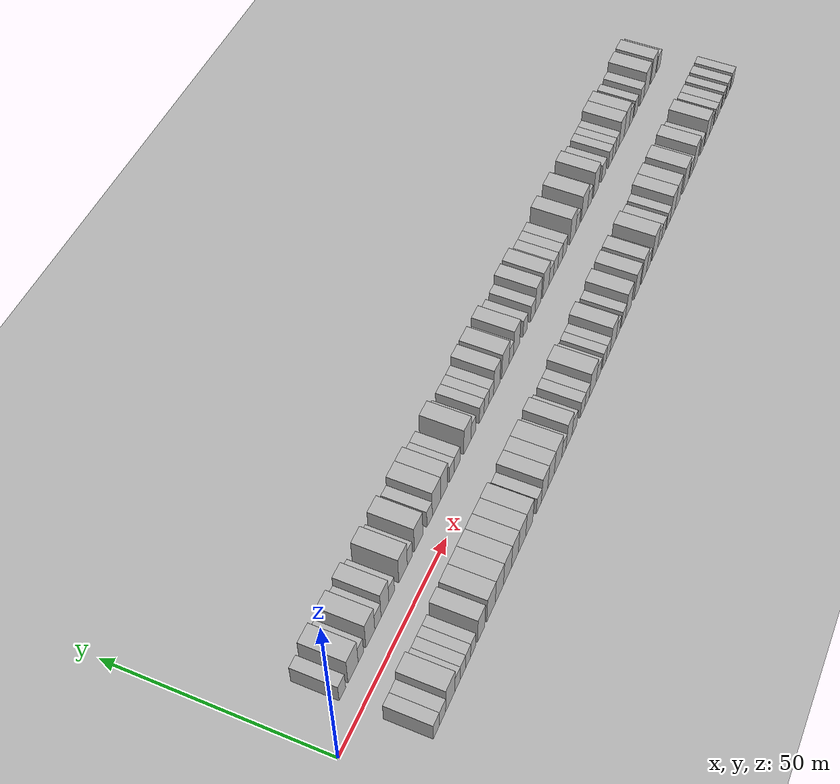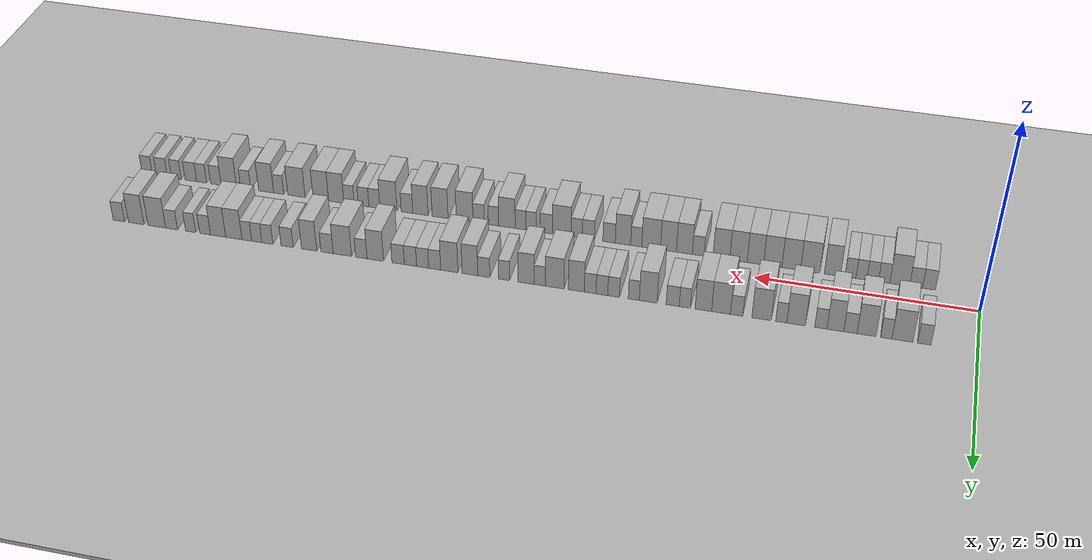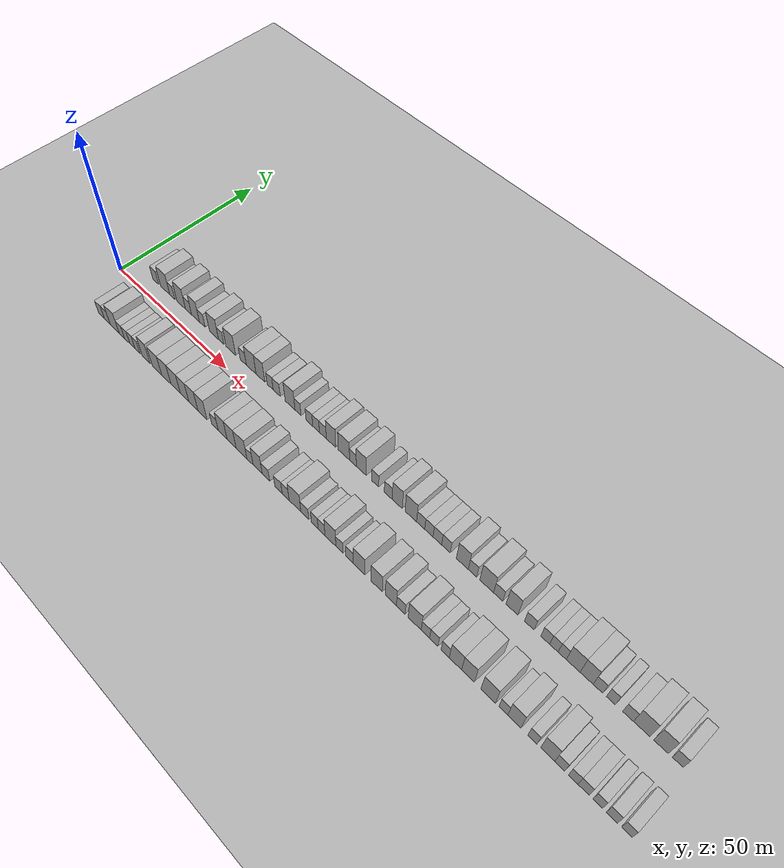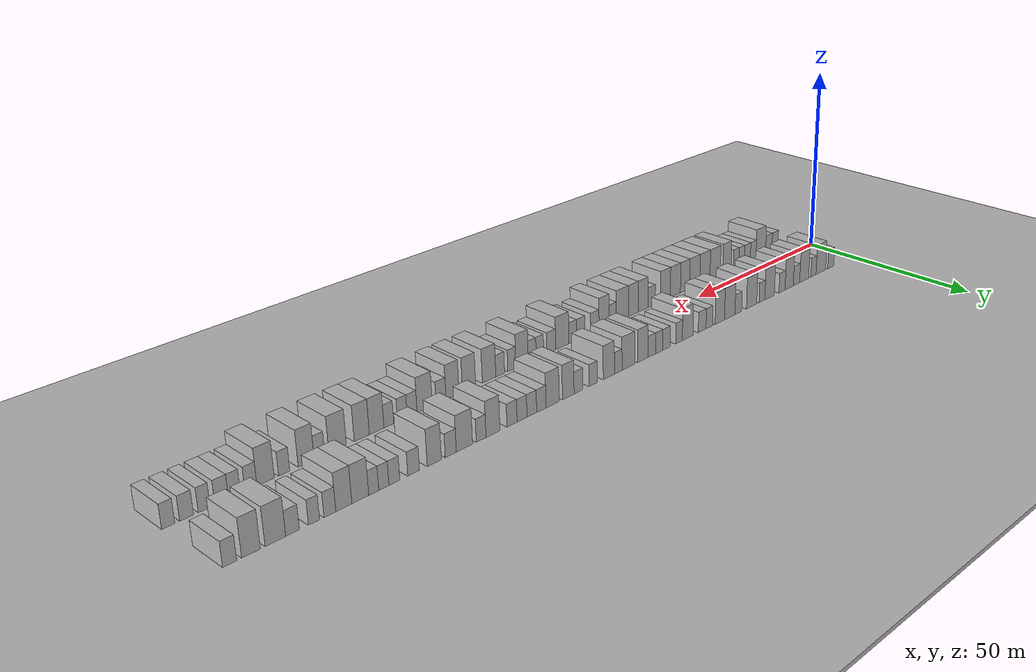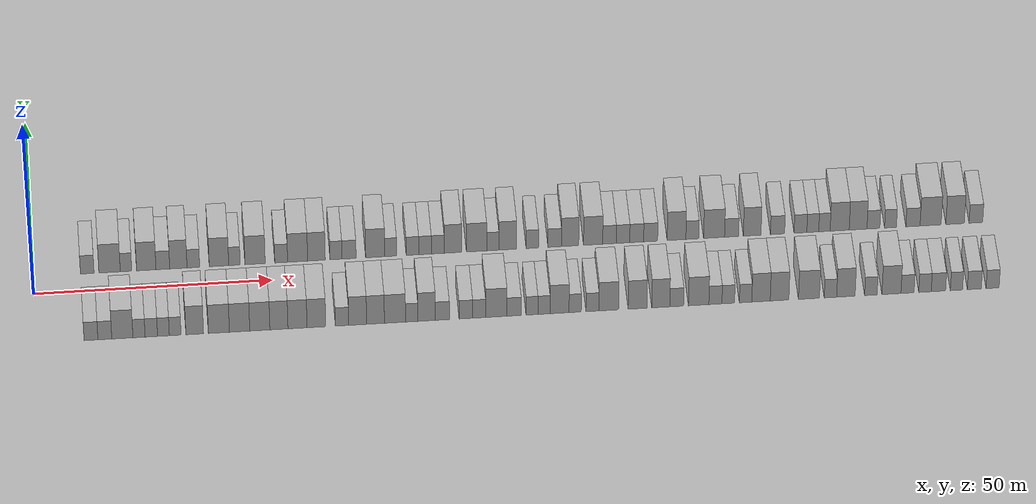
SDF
<?xml version="1.0" encoding="utf-8"?>

<sdf version="1.6">

   <world name="default">

      <gui fullscreen="0">

         <camera name="user_camera">

            <pose>-15 0 4.57585 0 0 0</pose>

            <view_controller>orbit</view_controller>

         </camera>

      </gui>

      <scene>

         <sky>

           <clouds>

             <speed>12</speed>

           </clouds>

         </sky>

         <ambient>0.4 0.4 0.4 1</ambient>

         <background>0.7 0.7 0.7 1</background>

         <shadows>1</shadows>

      </scene>

      <gravity>0 0 -9.8066</gravity>

      <magnetic_field>6e-06 2.3e-05 -4.2e-05</magnetic_field>

      <physics default="0" name="default_physics" type="ode">

         <ode>

            <solver>

               <type>quick</type>

               <iters>10</iters>

               <sor>1.0</sor>

               <use_dynamic_moi_rescaling>0</use_dynamic_moi_rescaling>

            </solver>

            <constraints>

               <cfm>0</cfm>

               <erp>0.2</erp>

               <contact_max_correcting_vel>100</contact_max_correcting_vel>

               <contact_surface_layer>0.001</contact_surface_layer>

            </constraints>

         </ode>

         <max_step_size>0.004</max_step_size>

         <real_time_factor>1</real_time_factor>

         <real_time_update_rate>250</real_time_update_rate>

      </physics>

      <light name="sun" type="directional">

         <cast_shadows>1</cast_shadows>

         <pose>0 0 10 0 0 0</pose>

         <diffuse>0.8 0.8 0.8 1</diffuse>

         <specular>0.2 0.2 0.2 1</specular>

         <attenuation>

            <range>1000</range>

            <constant>0.9</constant>

            <linear>0.01</linear>

            <quadratic>0.001</quadratic>

         </attenuation>

         <direction>-0.5 0.1 -0.9</direction>

      </light>

      <include>

         <name>ground_plane_1</name>

         <uri>model://HANNAS_ground_plane</uri>

         <pose>0 0 0  0 0 0</pose>

      </include>

      <include>

         <name>ground_plane_2</name>

         <uri>model://HANNAS_ground_plane</uri>

         <pose>100 0 0  0 0 0</pose>

      </include>

      <model name="building_1">

         <static>1</static>

         <pose frame="">11.4243 9.5000 0 0.000000 0.000000 1.570796</pose>

         <link name="link">

            <pose frame="">0 0 3.00 0 0 0</pose>

            <collision name="collision">

               <geometry>

                  <box>

                     <size>10.0000 2.8487 6.0000</size>

                  </box>

               </geometry>

               <max_contacts>10</max_contacts>

               <surface>

                  <contact>

                     <ode/>

                  </contact>

                  <bounce/>

                  <friction>

                     <torsional>

                        <ode/>

                     </torsional>

                     <ode/>

                  </friction>

               </surface>

            </collision>

            <visual name="visual">

               <cast_shadows>0</cast_shadows>

               <geometry>

                  <box>

                     <size>10.0000 2.8487 6.0000</size>

                  </box>

               </geometry>

               <material>

                  <script>

                     <uri>model://HANNAS_wall/materials/scripts</uri>

                     <uri>model://HANNAS_wall/materials/textures</uri>

                     <name>vrc/HANNAS_wall</name>

                  </script>

               </material>

            </visual>

            <self_collide>0</self_collide>

            <enable_wind>0</enable_wind>

            <kinematic>0</kinematic>

         </link>

      </model>

      <model name="building_2">

         <static>1</static>

         <pose frame="">16.0821 9.5000 0 0.000000 0.000000 1.570796</pose>

         <link name="link">

            <pose frame="">0 0 4.50 0 0 0</pose>

            <collision name="collision">

               <geometry>

                  <box>

                     <size>10.0000 4.4667 9.0000</size>

                  </box>

               </geometry>

               <max_contacts>10</max_contacts>

               <surface>

                  <contact>

                     <ode/>

                  </contact>

                  <bounce/>

                  <friction>

                     <torsional>

                        <ode/>

                     </torsional>

                     <ode/>

                  </friction>

               </surface>

            </collision>

            <visual name="visual">

               <cast_shadows>0</cast_shadows>

               <geometry>

                  <box>

                     <size>10.0000 4.4667 9.0000</size>

                  </box>

               </geometry>

               <material>

                  <script>

                     <uri>model://HANNAS_wall/materials/scripts</uri>

                     <uri>model://HANNAS_wall/materials/textures</uri>

                     <name>vrc/HANNAS_wall</name>

                  </script>

               </material>

            </visual>

            <self_collide>0</self_collide>

            <enable_wind>0</enable_wind>

            <kinematic>0</kinematic>

         </link>

      </model>

      <model name="building_3">

         <static>1</static>

         <pose frame="">19.5172 9.5000 0 0.000000 0.000000 1.570796</pose>

         <link name="link">

            <pose frame="">0 0 3.00 0 0 0</pose>

            <collision name="collision">

               <geometry>

                  <box>

                     <size>10.0000 2.4036 6.0000</size>

                  </box>

               </geometry>

               <max_contacts>10</max_contacts>

               <surface>

                  <contact>

                     <ode/>

                  </contact>

                  <bounce/>

                  <friction>

                     <torsional>

                        <ode/>

                     </torsional>

                     <ode/>

                  </friction>

               </surface>

            </collision>

            <visual name="visual">

               <cast_shadows>0</cast_shadows>

               <geometry>

                  <box>

                     <size>10.0000 2.4036 6.0000</size>

                  </box>

               </geometry>

               <material>

                  <script>

                     <uri>model://HANNAS_wall/materials/scripts</uri>

                     <uri>model://HANNAS_wall/materials/textures</uri>

                     <name>vrc/HANNAS_wall</name>

                  </script>

               </material>

            </visual>

            <self_collide>0</self_collide>

            <enable_wind>0</enable_wind>

            <kinematic>0</kinematic>

         </link>

      </model>

      <model name="building_4">

         <static>1</static>

         <pose frame="">23.7486 9.5000 0 0.000000 0.000000 1.570796</pose>

         <link name="link">

            <pose frame="">0 0 4.50 0 0 0</pose>

            <collision name="collision">

               <geometry>

                  <box>

                     <size>10.0000 4.0592 9.0000</size>

                  </box>

               </geometry>

               <max_contacts>10</max_contacts>

               <surface>

                  <contact>

                     <ode/>

                  </contact>

                  <bounce/>

                  <friction>

                     <torsional>

                        <ode/>

                     </torsional>

                     <ode/>

                  </friction>

               </surface>

            </collision>

            <visual name="visual">

               <cast_shadows>0</cast_shadows>

               <geometry>

                  <box>

                     <size>10.0000 4.0592 9.0000</size>

                  </box>

               </geometry>

               <material>

                  <script>

                     <uri>model://HANNAS_wall/materials/scripts</uri>

                     <uri>model://HANNAS_wall/materials/textures</uri>

                     <name>vrc/HANNAS_wall</name>

                  </script>

               </material>

            </visual>

            <self_collide>0</self_collide>

            <enable_wind>0</enable_wind>

            <kinematic>0</kinematic>

         </link>

      </model>

      <model name="building_5">

         <static>1</static>

         <pose frame="">27.2113 9.5000 0 0.000000 0.000000 1.570796</pose>

         <link name="link">

            <pose frame="">0 0 3.00 0 0 0</pose>

            <collision name="collision">

               <geometry>

                  <box>

                     <size>10.0000 2.8662 6.0000</size>

                  </box>

               </geometry>

               <max_contacts>10</max_contacts>

               <surface>

                  <contact>

                     <ode/>

                  </contact>

                  <bounce/>

                  <friction>

                     <torsional>

                        <ode/>

                     </torsional>

                     <ode/>

                  </friction>

               </surface>

            </collision>

            <visual name="visual">

               <cast_shadows>0</cast_shadows>

               <geometry>

                  <box>

                     <size>10.0000 2.8662 6.0000</size>

                  </box>

               </geometry>

               <material>

                  <script>

                     <uri>model://HANNAS_wall/materials/scripts</uri>

                     <uri>model://HANNAS_wall/materials/textures</uri>

                     <name>vrc/HANNAS_wall</name>

                  </script>

               </material>

            </visual>

            <self_collide>0</self_collide>

            <enable_wind>0</enable_wind>

            <kinematic>0</kinematic>

         </link>

      </model>

      <model name="building_6">

         <static>1</static>

         <pose frame="">30.4555 9.5000 0 0.000000 0.000000 1.570796</pose>

         <link name="link">

            <pose frame="">0 0 4.50 0 0 0</pose>

            <collision name="collision">

               <geometry>

                  <box>

                     <size>10.0000 3.6220 9.0000</size>

                  </box>

               </geometry>

               <max_contacts>10</max_contacts>

               <surface>

                  <contact>

                     <ode/>

                  </contact>

                  <bounce/>

                  <friction>

                     <torsional>

                        <ode/>

                     </torsional>

                     <ode/>

                  </friction>

               </surface>

            </collision>

            <visual name="visual">

               <cast_shadows>0</cast_shadows>

               <geometry>

                  <box>

                     <size>10.0000 3.6220 9.0000</size>

                  </box>

               </geometry>

               <material>

                  <script>

                     <uri>model://HANNAS_wall/materials/scripts</uri>

                     <uri>model://HANNAS_wall/materials/textures</uri>

                     <name>vrc/HANNAS_wall</name>

                  </script>

               </material>

            </visual>

            <self_collide>0</self_collide>

            <enable_wind>0</enable_wind>

            <kinematic>0</kinematic>

         </link>

      </model>

      <model name="building_7">

         <static>1</static>

         <pose frame="">33.5878 9.5000 0 0.000000 0.000000 1.570796</pose>

         <link name="link">

            <pose frame="">0 0 3.00 0 0 0</pose>

            <collision name="collision">

               <geometry>

                  <box>

                     <size>10.0000 2.6427 6.0000</size>

                  </box>

               </geometry>

               <max_contacts>10</max_contacts>

               <surface>

                  <contact>

                     <ode/>

                  </contact>

                  <bounce/>

                  <friction>

                     <torsional>

                        <ode/>

                     </torsional>

                     <ode/>

                  </friction>

               </surface>

            </collision>

            <visual name="visual">

               <cast_shadows>0</cast_shadows>

               <geometry>

                  <box>

                     <size>10.0000 2.6427 6.0000</size>

                  </box>

               </geometry>

               <material>

                  <script>

                     <uri>model://HANNAS_wall/materials/scripts</uri>

                     <uri>model://HANNAS_wall/materials/textures</uri>

                     <name>vrc/HANNAS_wall</name>

                  </script>

               </material>

            </visual>

            <self_collide>0</self_collide>

            <enable_wind>0</enable_wind>

            <kinematic>0</kinematic>

         </link>

      </model>

      <model name="building_8">

         <static>1</static>

         <pose frame="">38.9452 9.5000 0 0.000000 0.000000 1.570796</pose>

         <link name="link">

            <pose frame="">0 0 4.50 0 0 0</pose>

            <collision name="collision">

               <geometry>

                  <box>

                     <size>10.0000 4.0722 9.0000</size>

                  </box>

               </geometry>

               <max_contacts>10</max_contacts>

               <surface>

                  <contact>

                     <ode/>

                  </contact>

                  <bounce/>

                  <friction>

                     <torsional>

                        <ode/>

                     </torsional>

                     <ode/>

                  </friction>

               </surface>

            </collision>

            <visual name="visual">

               <cast_shadows>0</cast_shadows>

               <geometry>

                  <box>

                     <size>10.0000 4.0722 9.0000</size>

                  </box>

               </geometry>

               <material>

                  <script>

                     <uri>model://HANNAS_wall/materials/scripts</uri>

                     <uri>model://HANNAS_wall/materials/textures</uri>

                     <name>vrc/HANNAS_wall</name>

                  </script>

               </material>

            </visual>

            <self_collide>0</self_collide>

            <enable_wind>0</enable_wind>

            <kinematic>0</kinematic>

         </link>

      </model>

      <model name="building_9">

         <static>1</static>

         <pose frame="">42.1849 9.5000 0 0.000000 0.000000 1.570796</pose>

         <link name="link">

            <pose frame="">0 0 3.00 0 0 0</pose>

            <collision name="collision">

               <geometry>

                  <box>

                     <size>10.0000 2.4071 6.0000</size>

                  </box>

               </geometry>

               <max_contacts>10</max_contacts>

               <surface>

                  <contact>

                     <ode/>

                  </contact>

                  <bounce/>

                  <friction>

                     <torsional>

                        <ode/>

                     </torsional>

                     <ode/>

                  </friction>

               </surface>

            </collision>

            <visual name="visual">

               <cast_shadows>0</cast_shadows>

               <geometry>

                  <box>

                     <size>10.0000 2.4071 6.0000</size>

                  </box>

               </geometry>

               <material>

                  <script>

                     <uri>model://HANNAS_wall/materials/scripts</uri>

                     <uri>model://HANNAS_wall/materials/textures</uri>

                     <name>vrc/HANNAS_wall</name>

                  </script>

               </material>

            </visual>

            <self_collide>0</self_collide>

            <enable_wind>0</enable_wind>

            <kinematic>0</kinematic>

         </link>

      </model>

      <model name="building_10">

         <static>1</static>

         <pose frame="">46.5033 9.5000 0 0.000000 0.000000 1.570796</pose>

         <link name="link">

            <pose frame="">0 0 4.50 0 0 0</pose>

            <collision name="collision">

               <geometry>

                  <box>

                     <size>10.0000 4.2298 9.0000</size>

                  </box>

               </geometry>

               <max_contacts>10</max_contacts>

               <surface>

                  <contact>

                     <ode/>

                  </contact>

                  <bounce/>

                  <friction>

                     <torsional>

                        <ode/>

                     </torsional>

                     <ode/>

                  </friction>

               </surface>

            </collision>

            <visual name="visual">

               <cast_shadows>0</cast_shadows>

               <geometry>

                  <box>

                     <size>10.0000 4.2298 9.0000</size>

                  </box>

               </geometry>

               <material>

                  <script>

                     <uri>model://HANNAS_wall/materials/scripts</uri>

                     <uri>model://HANNAS_wall/materials/textures</uri>

                     <name>vrc/HANNAS_wall</name>

                  </script>

               </material>

            </visual>

            <self_collide>0</self_collide>

            <enable_wind>0</enable_wind>

            <kinematic>0</kinematic>

         </link>

      </model>

      <model name="building_11">

         <static>1</static>

         <pose frame="">51.9629 9.5000 0 0.000000 0.000000 1.570796</pose>

         <link name="link">

            <pose frame="">0 0 3.00 0 0 0</pose>

            <collision name="collision">

               <geometry>

                  <box>

                     <size>10.0000 2.6895 6.0000</size>

                  </box>

               </geometry>

               <max_contacts>10</max_contacts>

               <surface>

                  <contact>

                     <ode/>

                  </contact>

                  <bounce/>

                  <friction>

                     <torsional>

                        <ode/>

                     </torsional>

                     <ode/>

                  </friction>

               </surface>

            </collision>

            <visual name="visual">

               <cast_shadows>0</cast_shadows>

               <geometry>

                  <box>

                     <size>10.0000 2.6895 6.0000</size>

                  </box>

               </geometry>

               <material>

                  <script>

                     <uri>model://HANNAS_wall/materials/scripts</uri>

                     <uri>model://HANNAS_wall/materials/textures</uri>

                     <name>vrc/HANNAS_wall</name>

                  </script>

               </material>

            </visual>

            <self_collide>0</self_collide>

            <enable_wind>0</enable_wind>

            <kinematic>0</kinematic>

         </link>

      </model>

      <model name="building_12">

         <static>1</static>

         <pose frame="">55.4036 9.5000 0 0.000000 0.000000 1.570796</pose>

         <link name="link">

            <pose frame="">0 0 4.50 0 0 0</pose>

            <collision name="collision">

               <geometry>

                  <box>

                     <size>10.0000 4.1919 9.0000</size>

                  </box>

               </geometry>

               <max_contacts>10</max_contacts>

               <surface>

                  <contact>

                     <ode/>

                  </contact>

                  <bounce/>

                  <friction>

                     <torsional>

                        <ode/>

                     </torsional>

                     <ode/>

                  </friction>

               </surface>

            </collision>

            <visual name="visual">

               <cast_shadows>0</cast_shadows>

               <geometry>

                  <box>

                     <size>10.0000 4.1919 9.0000</size>

                  </box>

               </geometry>

               <material>

                  <script>

                     <uri>model://HANNAS_wall/materials/scripts</uri>

                     <uri>model://HANNAS_wall/materials/textures</uri>

                     <name>vrc/HANNAS_wall</name>

                  </script>

               </material>

            </visual>

            <self_collide>0</self_collide>

            <enable_wind>0</enable_wind>

            <kinematic>0</kinematic>

         </link>

      </model>

      <model name="building_13">

         <static>1</static>

         <pose frame="">59.3472 9.5000 0 0.000000 0.000000 1.570796</pose>

         <link name="link">

            <pose frame="">0 0 4.50 0 0 0</pose>

            <collision name="collision">

               <geometry>

                  <box>

                     <size>10.0000 3.6953 9.0000</size>

                  </box>

               </geometry>

               <max_contacts>10</max_contacts>

               <surface>

                  <contact>

                     <ode/>

                  </contact>

                  <bounce/>

                  <friction>

                     <torsional>

                        <ode/>

                     </torsional>

                     <ode/>

                  </friction>

               </surface>

            </collision>

            <visual name="visual">

               <cast_shadows>0</cast_shadows>

               <geometry>

                  <box>

                     <size>10.0000 3.6953 9.0000</size>

                  </box>

               </geometry>

               <material>

                  <script>

                     <uri>model://HANNAS_wall/materials/scripts</uri>

                     <uri>model://HANNAS_wall/materials/textures</uri>

                     <name>vrc/HANNAS_wall</name>

                  </script>

               </material>

            </visual>

            <self_collide>0</self_collide>

            <enable_wind>0</enable_wind>

            <kinematic>0</kinematic>

         </link>

      </model>

      <model name="building_14">

         <static>1</static>

         <pose frame="">63.4480 9.5000 0 0.000000 0.000000 1.570796</pose>

         <link name="link">

            <pose frame="">0 0 3.00 0 0 0</pose>

            <collision name="collision">

               <geometry>

                  <box>

                     <size>10.0000 2.5064 6.0000</size>

                  </box>

               </geometry>

               <max_contacts>10</max_contacts>

               <surface>

                  <contact>

                     <ode/>

                  </contact>

                  <bounce/>

                  <friction>

                     <torsional>

                        <ode/>

                     </torsional>

                     <ode/>

                  </friction>

               </surface>

            </collision>

            <visual name="visual">

               <cast_shadows>0</cast_shadows>

               <geometry>

                  <box>

                     <size>10.0000 2.5064 6.0000</size>

                  </box>

               </geometry>

               <material>

                  <script>

                     <uri>model://HANNAS_wall/materials/scripts</uri>

                     <uri>model://HANNAS_wall/materials/textures</uri>

                     <name>vrc/HANNAS_wall</name>

                  </script>

               </material>

            </visual>

            <self_collide>0</self_collide>

            <enable_wind>0</enable_wind>

            <kinematic>0</kinematic>

         </link>

      </model>

      <model name="building_15">

         <static>1</static>

         <pose frame="">66.1786 9.5000 0 0.000000 0.000000 1.570796</pose>

         <link name="link">

            <pose frame="">0 0 3.00 0 0 0</pose>

            <collision name="collision">

               <geometry>

                  <box>

                     <size>10.0000 2.9547 6.0000</size>

                  </box>

               </geometry>

               <max_contacts>10</max_contacts>

               <surface>

                  <contact>

                     <ode/>

                  </contact>

                  <bounce/>

                  <friction>

                     <torsional>

                        <ode/>

                     </torsional>

                     <ode/>

                  </friction>

               </surface>

            </collision>

            <visual name="visual">

               <cast_shadows>0</cast_shadows>

               <geometry>

                  <box>

                     <size>10.0000 2.9547 6.0000</size>

                  </box>

               </geometry>

               <material>

                  <script>

                     <uri>model://HANNAS_wall/materials/scripts</uri>

                     <uri>model://HANNAS_wall/materials/textures</uri>

                     <name>vrc/HANNAS_wall</name>

                  </script>

               </material>

            </visual>

            <self_collide>0</self_collide>

            <enable_wind>0</enable_wind>

            <kinematic>0</kinematic>

         </link>

      </model>

      <model name="building_16">

         <static>1</static>

         <pose frame="">71.6611 9.5000 0 0.000000 0.000000 1.570796</pose>

         <link name="link">

            <pose frame="">0 0 4.50 0 0 0</pose>

            <collision name="collision">

               <geometry>

                  <box>

                     <size>10.0000 4.0103 9.0000</size>

                  </box>

               </geometry>

               <max_contacts>10</max_contacts>

               <surface>

                  <contact>

                     <ode/>

                  </contact>

                  <bounce/>

                  <friction>

                     <torsional>

                        <ode/>

                     </torsional>

                     <ode/>

                  </friction>

               </surface>

            </collision>

            <visual name="visual">

               <cast_shadows>0</cast_shadows>

               <geometry>

                  <box>

                     <size>10.0000 4.0103 9.0000</size>

                  </box>

               </geometry>

               <material>

                  <script>

                     <uri>model://HANNAS_wall/materials/scripts</uri>

                     <uri>model://HANNAS_wall/materials/textures</uri>

                     <name>vrc/HANNAS_wall</name>

                  </script>

               </material>

            </visual>

            <self_collide>0</self_collide>

            <enable_wind>0</enable_wind>

            <kinematic>0</kinematic>

         </link>

      </model>

      <model name="building_17">

         <static>1</static>

         <pose frame="">74.9075 9.5000 0 0.000000 0.000000 1.570796</pose>

         <link name="link">

            <pose frame="">0 0 3.00 0 0 0</pose>

            <collision name="collision">

               <geometry>

                  <box>

                     <size>10.0000 2.4826 6.0000</size>

                  </box>

               </geometry>

               <max_contacts>10</max_contacts>

               <surface>

                  <contact>

                     <ode/>

                  </contact>

                  <bounce/>

                  <friction>

                     <torsional>

                        <ode/>

                     </torsional>

                     <ode/>

                  </friction>

               </surface>

            </collision>

            <visual name="visual">

               <cast_shadows>0</cast_shadows>

               <geometry>

                  <box>

                     <size>10.0000 2.4826 6.0000</size>

                  </box>

               </geometry>

               <material>

                  <script>

                     <uri>model://HANNAS_wall/materials/scripts</uri>

                     <uri>model://HANNAS_wall/materials/textures</uri>

                     <name>vrc/HANNAS_wall</name>

                  </script>

               </material>

            </visual>

            <self_collide>0</self_collide>

            <enable_wind>0</enable_wind>

            <kinematic>0</kinematic>

         </link>

      </model>

      <model name="building_18">

         <static>1</static>

         <pose frame="">79.4755 9.5000 0 0.000000 0.000000 1.570796</pose>

         <link name="link">

            <pose frame="">0 0 3.00 0 0 0</pose>

            <collision name="collision">

               <geometry>

                  <box>

                     <size>10.0000 2.6533 6.0000</size>

                  </box>

               </geometry>

               <max_contacts>10</max_contacts>

               <surface>

                  <contact>

                     <ode/>

                  </contact>

                  <bounce/>

                  <friction>

                     <torsional>

                        <ode/>

                     </torsional>

                     <ode/>

                  </friction>

               </surface>

            </collision>

            <visual name="visual">

               <cast_shadows>0</cast_shadows>

               <geometry>

                  <box>

                     <size>10.0000 2.6533 6.0000</size>

                  </box>

               </geometry>

               <material>

                  <script>

                     <uri>model://HANNAS_wall/materials/scripts</uri>

                     <uri>model://HANNAS_wall/materials/textures</uri>

                     <name>vrc/HANNAS_wall</name>

                  </script>

               </material>

            </visual>

            <self_collide>0</self_collide>

            <enable_wind>0</enable_wind>

            <kinematic>0</kinematic>

         </link>

      </model>

      <model name="building_19">

         <static>1</static>

         <pose frame="">82.1273 9.5000 0 0.000000 0.000000 1.570796</pose>

         <link name="link">

            <pose frame="">0 0 3.00 0 0 0</pose>

            <collision name="collision">

               <geometry>

                  <box>

                     <size>10.0000 2.6502 6.0000</size>

                  </box>

               </geometry>

               <max_contacts>10</max_contacts>

               <surface>

                  <contact>

                     <ode/>

                  </contact>

                  <bounce/>

                  <friction>

                     <torsional>

                        <ode/>

                     </torsional>

                     <ode/>

                  </friction>

               </surface>

            </collision>

            <visual name="visual">

               <cast_shadows>0</cast_shadows>

               <geometry>

                  <box>

                     <size>10.0000 2.6502 6.0000</size>

                  </box>

               </geometry>

               <material>

                  <script>

                     <uri>model://HANNAS_wall/materials/scripts</uri>

                     <uri>model://HANNAS_wall/materials/textures</uri>

                     <name>vrc/HANNAS_wall</name>

                  </script>

               </material>

            </visual>

            <self_collide>0</self_collide>

            <enable_wind>0</enable_wind>

            <kinematic>0</kinematic>

         </link>

      </model>

      <model name="building_20">

         <static>1</static>

         <pose frame="">84.7963 9.5000 0 0.000000 0.000000 1.570796</pose>

         <link name="link">

            <pose frame="">0 0 3.00 0 0 0</pose>

            <collision name="collision">

               <geometry>

                  <box>

                     <size>10.0000 2.6878 6.0000</size>

                  </box>

               </geometry>

               <max_contacts>10</max_contacts>

               <surface>

                  <contact>

                     <ode/>

                  </contact>

                  <bounce/>

                  <friction>

                     <torsional>

                        <ode/>

                     </torsional>

                     <ode/>

                  </friction>

               </surface>

            </collision>

            <visual name="visual">

               <cast_shadows>0</cast_shadows>

               <geometry>

                  <box>

                     <size>10.0000 2.6878 6.0000</size>

                  </box>

               </geometry>

               <material>

                  <script>

                     <uri>model://HANNAS_wall/materials/scripts</uri>

                     <uri>model://HANNAS_wall/materials/textures</uri>

                     <name>vrc/HANNAS_wall</name>

                  </script>

               </material>

            </visual>

            <self_collide>0</self_collide>

            <enable_wind>0</enable_wind>

            <kinematic>0</kinematic>

         </link>

      </model>

      <model name="building_21">

         <static>1</static>

         <pose frame="">87.9609 9.5000 0 0.000000 0.000000 1.570796</pose>

         <link name="link">

            <pose frame="">0 0 4.50 0 0 0</pose>

            <collision name="collision">

               <geometry>

                  <box>

                     <size>10.0000 3.6413 9.0000</size>

                  </box>

               </geometry>

               <max_contacts>10</max_contacts>

               <surface>

                  <contact>

                     <ode/>

                  </contact>

                  <bounce/>

                  <friction>

                     <torsional>

                        <ode/>

                     </torsional>

                     <ode/>

                  </friction>

               </surface>

            </collision>

            <visual name="visual">

               <cast_shadows>0</cast_shadows>

               <geometry>

                  <box>

                     <size>10.0000 3.6413 9.0000</size>

                  </box>

               </geometry>

               <material>

                  <script>

                     <uri>model://HANNAS_wall/materials/scripts</uri>

                     <uri>model://HANNAS_wall/materials/textures</uri>

                     <name>vrc/HANNAS_wall</name>

                  </script>

               </material>

            </visual>

            <self_collide>0</self_collide>

            <enable_wind>0</enable_wind>

            <kinematic>0</kinematic>

         </link>

      </model>

      <model name="building_22">

         <static>1</static>

         <pose frame="">92.9177 9.5000 0 0.000000 0.000000 1.570796</pose>

         <link name="link">

            <pose frame="">0 0 4.50 0 0 0</pose>

            <collision name="collision">

               <geometry>

                  <box>

                     <size>10.0000 4.2722 9.0000</size>

                  </box>

               </geometry>

               <max_contacts>10</max_contacts>

               <surface>

                  <contact>

                     <ode/>

                  </contact>

                  <bounce/>

                  <friction>

                     <torsional>

                        <ode/>

                     </torsional>

                     <ode/>

                  </friction>

               </surface>

            </collision>

            <visual name="visual">

               <cast_shadows>0</cast_shadows>

               <geometry>

                  <box>

                     <size>10.0000 4.2722 9.0000</size>

                  </box>

               </geometry>

               <material>

                  <script>

                     <uri>model://HANNAS_wall/materials/scripts</uri>

                     <uri>model://HANNAS_wall/materials/textures</uri>

                     <name>vrc/HANNAS_wall</name>

                  </script>

               </material>

            </visual>

            <self_collide>0</self_collide>

            <enable_wind>0</enable_wind>

            <kinematic>0</kinematic>

         </link>

      </model>

      <model name="building_23">

         <static>1</static>

         <pose frame="">96.3327 9.5000 0 0.000000 0.000000 1.570796</pose>

         <link name="link">

            <pose frame="">0 0 3.00 0 0 0</pose>

            <collision name="collision">

               <geometry>

                  <box>

                     <size>10.0000 2.5578 6.0000</size>

                  </box>

               </geometry>

               <max_contacts>10</max_contacts>

               <surface>

                  <contact>

                     <ode/>

                  </contact>

                  <bounce/>

                  <friction>

                     <torsional>

                        <ode/>

                     </torsional>

                     <ode/>

                  </friction>

               </surface>

            </collision>

            <visual name="visual">

               <cast_shadows>0</cast_shadows>

               <geometry>

                  <box>

                     <size>10.0000 2.5578 6.0000</size>

                  </box>

               </geometry>

               <material>

                  <script>

                     <uri>model://HANNAS_wall/materials/scripts</uri>

                     <uri>model://HANNAS_wall/materials/textures</uri>

                     <name>vrc/HANNAS_wall</name>

                  </script>

               </material>

            </visual>

            <self_collide>0</self_collide>

            <enable_wind>0</enable_wind>

            <kinematic>0</kinematic>

         </link>

      </model>

      <model name="building_24">

         <static>1</static>

         <pose frame="">99.4689 9.5000 0 0.000000 0.000000 1.570796</pose>

         <link name="link">

            <pose frame="">0 0 4.50 0 0 0</pose>

            <collision name="collision">

               <geometry>

                  <box>

                     <size>10.0000 3.7147 9.0000</size>

                  </box>

               </geometry>

               <max_contacts>10</max_contacts>

               <surface>

                  <contact>

                     <ode/>

                  </contact>

                  <bounce/>

                  <friction>

                     <torsional>

                        <ode/>

                     </torsional>

                     <ode/>

                  </friction>

               </surface>

            </collision>

            <visual name="visual">

               <cast_shadows>0</cast_shadows>

               <geometry>

                  <box>

                     <size>10.0000 3.7147 9.0000</size>

                  </box>

               </geometry>

               <material>

                  <script>

                     <uri>model://HANNAS_wall/materials/scripts</uri>

                     <uri>model://HANNAS_wall/materials/textures</uri>

                     <name>vrc/HANNAS_wall</name>

                  </script>

               </material>

            </visual>

            <self_collide>0</self_collide>

            <enable_wind>0</enable_wind>

            <kinematic>0</kinematic>

         </link>

      </model>

      <model name="building_25">

         <static>1</static>

         <pose frame="">104.6225 9.5000 0 0.000000 0.000000 1.570796</pose>

         <link name="link">

            <pose frame="">0 0 3.00 0 0 0</pose>

            <collision name="collision">

               <geometry>

                  <box>

                     <size>10.0000 2.5924 6.0000</size>

                  </box>

               </geometry>

               <max_contacts>10</max_contacts>

               <surface>

                  <contact>

                     <ode/>

                  </contact>

                  <bounce/>

                  <friction>

                     <torsional>

                        <ode/>

                     </torsional>

                     <ode/>

                  </friction>

               </surface>

            </collision>

            <visual name="visual">

               <cast_shadows>0</cast_shadows>

               <geometry>

                  <box>

                     <size>10.0000 2.5924 6.0000</size>

                  </box>

               </geometry>

               <material>

                  <script>

                     <uri>model://HANNAS_wall/materials/scripts</uri>

                     <uri>model://HANNAS_wall/materials/textures</uri>

                     <name>vrc/HANNAS_wall</name>

                  </script>

               </material>

            </visual>

            <self_collide>0</self_collide>

            <enable_wind>0</enable_wind>

            <kinematic>0</kinematic>

         </link>

      </model>

      <model name="building_26">

         <static>1</static>

         <pose frame="">109.3335 9.5000 0 0.000000 0.000000 1.570796</pose>

         <link name="link">

            <pose frame="">0 0 3.00 0 0 0</pose>

            <collision name="collision">

               <geometry>

                  <box>

                     <size>10.0000 2.8296 6.0000</size>

                  </box>

               </geometry>

               <max_contacts>10</max_contacts>

               <surface>

                  <contact>

                     <ode/>

                  </contact>

                  <bounce/>

                  <friction>

                     <torsional>

                        <ode/>

                     </torsional>

                     <ode/>

                  </friction>

               </surface>

            </collision>

            <visual name="visual">

               <cast_shadows>0</cast_shadows>

               <geometry>

                  <box>

                     <size>10.0000 2.8296 6.0000</size>

                  </box>

               </geometry>

               <material>

                  <script>

                     <uri>model://HANNAS_wall/materials/scripts</uri>

                     <uri>model://HANNAS_wall/materials/textures</uri>

                     <name>vrc/HANNAS_wall</name>

                  </script>

               </material>

            </visual>

            <self_collide>0</self_collide>

            <enable_wind>0</enable_wind>

            <kinematic>0</kinematic>

         </link>

      </model>

      <model name="building_27">

         <static>1</static>

         <pose frame="">112.5689 9.5000 0 0.000000 0.000000 1.570796</pose>

         <link name="link">

            <pose frame="">0 0 4.50 0 0 0</pose>

            <collision name="collision">

               <geometry>

                  <box>

                     <size>10.0000 3.6413 9.0000</size>

                  </box>

               </geometry>

               <max_contacts>10</max_contacts>

               <surface>

                  <contact>

                     <ode/>

                  </contact>

                  <bounce/>

                  <friction>

                     <torsional>

                        <ode/>

                     </torsional>

                     <ode/>

                  </friction>

               </surface>

            </collision>

            <visual name="visual">

               <cast_shadows>0</cast_shadows>

               <geometry>

                  <box>

                     <size>10.0000 3.6413 9.0000</size>

                  </box>

               </geometry>

               <material>

                  <script>

                     <uri>model://HANNAS_wall/materials/scripts</uri>

                     <uri>model://HANNAS_wall/materials/textures</uri>

                     <name>vrc/HANNAS_wall</name>

                  </script>

               </material>

            </visual>

            <self_collide>0</self_collide>

            <enable_wind>0</enable_wind>

            <kinematic>0</kinematic>

         </link>

      </model>

      <model name="building_28">

         <static>1</static>

         <pose frame="">117.4091 9.5000 0 0.000000 0.000000 1.570796</pose>

         <link name="link">

            <pose frame="">0 0 4.50 0 0 0</pose>

            <collision name="collision">

               <geometry>

                  <box>

                     <size>10.0000 4.0390 9.0000</size>

                  </box>

               </geometry>

               <max_contacts>10</max_contacts>

               <surface>

                  <contact>

                     <ode/>

                  </contact>

                  <bounce/>

                  <friction>

                     <torsional>

                        <ode/>

                     </torsional>

                     <ode/>

                  </friction>

               </surface>

            </collision>

            <visual name="visual">

               <cast_shadows>0</cast_shadows>

               <geometry>

                  <box>

                     <size>10.0000 4.0390 9.0000</size>

                  </box>

               </geometry>

               <material>

                  <script>

                     <uri>model://HANNAS_wall/materials/scripts</uri>

                     <uri>model://HANNAS_wall/materials/textures</uri>

                     <name>vrc/HANNAS_wall</name>

                  </script>

               </material>

            </visual>

            <self_collide>0</self_collide>

            <enable_wind>0</enable_wind>

            <kinematic>0</kinematic>

         </link>

      </model>

      <model name="building_29">

         <static>1</static>

         <pose frame="">120.8455 9.5000 0 0.000000 0.000000 1.570796</pose>

         <link name="link">

            <pose frame="">0 0 3.00 0 0 0</pose>

            <collision name="collision">

               <geometry>

                  <box>

                     <size>10.0000 2.8339 6.0000</size>

                  </box>

               </geometry>

               <max_contacts>10</max_contacts>

               <surface>

                  <contact>

                     <ode/>

                  </contact>

                  <bounce/>

                  <friction>

                     <torsional>

                        <ode/>

                     </torsional>

                     <ode/>

                  </friction>

               </surface>

            </collision>

            <visual name="visual">

               <cast_shadows>0</cast_shadows>

               <geometry>

                  <box>

                     <size>10.0000 2.8339 6.0000</size>

                  </box>

               </geometry>

               <material>

                  <script>

                     <uri>model://HANNAS_wall/materials/scripts</uri>

                     <uri>model://HANNAS_wall/materials/textures</uri>

                     <name>vrc/HANNAS_wall</name>

                  </script>

               </material>

            </visual>

            <self_collide>0</self_collide>

            <enable_wind>0</enable_wind>

            <kinematic>0</kinematic>

         </link>

      </model>

      <model name="building_30">

         <static>1</static>

         <pose frame="">123.6905 9.5000 0 0.000000 0.000000 1.570796</pose>

         <link name="link">

            <pose frame="">0 0 3.00 0 0 0</pose>

            <collision name="collision">

               <geometry>

                  <box>

                     <size>10.0000 2.8562 6.0000</size>

                  </box>

               </geometry>

               <max_contacts>10</max_contacts>

               <surface>

                  <contact>

                     <ode/>

                  </contact>

                  <bounce/>

                  <friction>

                     <torsional>

                        <ode/>

                     </torsional>

                     <ode/>

                  </friction>

               </surface>

            </collision>

            <visual name="visual">

               <cast_shadows>0</cast_shadows>

               <geometry>

                  <box>

                     <size>10.0000 2.8562 6.0000</size>

                  </box>

               </geometry>

               <material>

                  <script>

                     <uri>model://HANNAS_wall/materials/scripts</uri>

                     <uri>model://HANNAS_wall/materials/textures</uri>

                     <name>vrc/HANNAS_wall</name>

                  </script>

               </material>

            </visual>

            <self_collide>0</self_collide>

            <enable_wind>0</enable_wind>

            <kinematic>0</kinematic>

         </link>

      </model>

      <model name="building_31">

         <static>1</static>

         <pose frame="">126.5782 9.5000 0 0.000000 0.000000 1.570796</pose>

         <link name="link">

            <pose frame="">0 0 3.00 0 0 0</pose>

            <collision name="collision">

               <geometry>

                  <box>

                     <size>10.0000 2.9191 6.0000</size>

                  </box>

               </geometry>

               <max_contacts>10</max_contacts>

               <surface>

                  <contact>

                     <ode/>

                  </contact>

                  <bounce/>

                  <friction>

                     <torsional>

                        <ode/>

                     </torsional>

                     <ode/>

                  </friction>

               </surface>

            </collision>

            <visual name="visual">

               <cast_shadows>0</cast_shadows>

               <geometry>

                  <box>

                     <size>10.0000 2.9191 6.0000</size>

                  </box>

               </geometry>

               <material>

                  <script>

                     <uri>model://HANNAS_wall/materials/scripts</uri>

                     <uri>model://HANNAS_wall/materials/textures</uri>

                     <name>vrc/HANNAS_wall</name>

                  </script>

               </material>

            </visual>

            <self_collide>0</self_collide>

            <enable_wind>0</enable_wind>

            <kinematic>0</kinematic>

         </link>

      </model>

      <model name="building_32">

         <static>1</static>

         <pose frame="">129.5099 9.5000 0 0.000000 0.000000 1.570796</pose>

         <link name="link">

            <pose frame="">0 0 3.00 0 0 0</pose>

            <collision name="collision">

               <geometry>

                  <box>

                     <size>10.0000 2.9444 6.0000</size>

                  </box>

               </geometry>

               <max_contacts>10</max_contacts>

               <surface>

                  <contact>

                     <ode/>

                  </contact>

                  <bounce/>

                  <friction>

                     <torsional>

                        <ode/>

                     </torsional>

                     <ode/>

                  </friction>

               </surface>

            </collision>

            <visual name="visual">

               <cast_shadows>0</cast_shadows>

               <geometry>

                  <box>

                     <size>10.0000 2.9444 6.0000</size>

                  </box>

               </geometry>

               <material>

                  <script>

                     <uri>model://HANNAS_wall/materials/scripts</uri>

                     <uri>model://HANNAS_wall/materials/textures</uri>

                     <name>vrc/HANNAS_wall</name>

                  </script>

               </material>

            </visual>

            <self_collide>0</self_collide>

            <enable_wind>0</enable_wind>

            <kinematic>0</kinematic>

         </link>

      </model>

      <model name="building_33">

         <static>1</static>

         <pose frame="">134.9548 9.5000 0 0.000000 0.000000 1.570796</pose>

         <link name="link">

            <pose frame="">0 0 4.50 0 0 0</pose>

            <collision name="collision">

               <geometry>

                  <box>

                     <size>10.0000 3.9455 9.0000</size>

                  </box>

               </geometry>

               <max_contacts>10</max_contacts>

               <surface>

                  <contact>

                     <ode/>

                  </contact>

                  <bounce/>

                  <friction>

                     <torsional>

                        <ode/>

                     </torsional>

                     <ode/>

                  </friction>

               </surface>

            </collision>

            <visual name="visual">

               <cast_shadows>0</cast_shadows>

               <geometry>

                  <box>

                     <size>10.0000 3.9455 9.0000</size>

                  </box>

               </geometry>

               <material>

                  <script>

                     <uri>model://HANNAS_wall/materials/scripts</uri>

                     <uri>model://HANNAS_wall/materials/textures</uri>

                     <name>vrc/HANNAS_wall</name>

                  </script>

               </material>

            </visual>

            <self_collide>0</self_collide>

            <enable_wind>0</enable_wind>

            <kinematic>0</kinematic>

         </link>

      </model>

      <model name="building_34">

         <static>1</static>

         <pose frame="">138.2891 9.5000 0 0.000000 0.000000 1.570796</pose>

         <link name="link">

            <pose frame="">0 0 3.00 0 0 0</pose>

            <collision name="collision">

               <geometry>

                  <box>

                     <size>10.0000 2.7231 6.0000</size>

                  </box>

               </geometry>

               <max_contacts>10</max_contacts>

               <surface>

                  <contact>

                     <ode/>

                  </contact>

                  <bounce/>

                  <friction>

                     <torsional>

                        <ode/>

                     </torsional>

                     <ode/>

                  </friction>

               </surface>

            </collision>

            <visual name="visual">

               <cast_shadows>0</cast_shadows>

               <geometry>

                  <box>

                     <size>10.0000 2.7231 6.0000</size>

                  </box>

               </geometry>

               <material>

                  <script>

                     <uri>model://HANNAS_wall/materials/scripts</uri>

                     <uri>model://HANNAS_wall/materials/textures</uri>

                     <name>vrc/HANNAS_wall</name>

                  </script>

               </material>

            </visual>

            <self_collide>0</self_collide>

            <enable_wind>0</enable_wind>

            <kinematic>0</kinematic>

         </link>

      </model>

      <model name="building_35">

         <static>1</static>

         <pose frame="">142.8634 9.5000 0 0.000000 0.000000 1.570796</pose>

         <link name="link">

            <pose frame="">0 0 4.50 0 0 0</pose>

            <collision name="collision">

               <geometry>

                  <box>

                     <size>10.0000 4.4256 9.0000</size>

                  </box>

               </geometry>

               <max_contacts>10</max_contacts>

               <surface>

                  <contact>

                     <ode/>

                  </contact>

                  <bounce/>

                  <friction>

                     <torsional>

                        <ode/>

                     </torsional>

                     <ode/>

                  </friction>

               </surface>

            </collision>

            <visual name="visual">

               <cast_shadows>0</cast_shadows>

               <geometry>

                  <box>

                     <size>10.0000 4.4256 9.0000</size>

                  </box>

               </geometry>

               <material>

                  <script>

                     <uri>model://HANNAS_wall/materials/scripts</uri>

                     <uri>model://HANNAS_wall/materials/textures</uri>

                     <name>vrc/HANNAS_wall</name>

                  </script>

               </material>

            </visual>

            <self_collide>0</self_collide>

            <enable_wind>0</enable_wind>

            <kinematic>0</kinematic>

         </link>

      </model>

      <model name="building_36">

         <static>1</static>

         <pose frame="">146.5519 9.5000 0 0.000000 0.000000 1.570796</pose>

         <link name="link">

            <pose frame="">0 0 3.00 0 0 0</pose>

            <collision name="collision">

               <geometry>

                  <box>

                     <size>10.0000 2.9514 6.0000</size>

                  </box>

               </geometry>

               <max_contacts>10</max_contacts>

               <surface>

                  <contact>

                     <ode/>

                  </contact>

                  <bounce/>

                  <friction>

                     <torsional>

                        <ode/>

                     </torsional>

                     <ode/>

                  </friction>

               </surface>

            </collision>

            <visual name="visual">

               <cast_shadows>0</cast_shadows>

               <geometry>

                  <box>

                     <size>10.0000 2.9514 6.0000</size>

                  </box>

               </geometry>

               <material>

                  <script>

                     <uri>model://HANNAS_wall/materials/scripts</uri>

                     <uri>model://HANNAS_wall/materials/textures</uri>

                     <name>vrc/HANNAS_wall</name>

                  </script>

               </material>

            </visual>

            <self_collide>0</self_collide>

            <enable_wind>0</enable_wind>

            <kinematic>0</kinematic>

         </link>

      </model>

      <model name="building_37">

         <static>1</static>

         <pose frame="">150.8884 9.5000 0 0.000000 0.000000 1.570796</pose>

         <link name="link">

            <pose frame="">0 0 4.50 0 0 0</pose>

            <collision name="collision">

               <geometry>

                  <box>

                     <size>10.0000 3.7215 9.0000</size>

                  </box>

               </geometry>

               <max_contacts>10</max_contacts>

               <surface>

                  <contact>

                     <ode/>

                  </contact>

                  <bounce/>

                  <friction>

                     <torsional>

                        <ode/>

                     </torsional>

                     <ode/>

                  </friction>

               </surface>

            </collision>

            <visual name="visual">

               <cast_shadows>0</cast_shadows>

               <geometry>

                  <box>

                     <size>10.0000 3.7215 9.0000</size>

                  </box>

               </geometry>

               <material>

                  <script>

                     <uri>model://HANNAS_wall/materials/scripts</uri>

                     <uri>model://HANNAS_wall/materials/textures</uri>

                     <name>vrc/HANNAS_wall</name>

                  </script>

               </material>

            </visual>

            <self_collide>0</self_collide>

            <enable_wind>0</enable_wind>

            <kinematic>0</kinematic>

         </link>

      </model>

      <model name="building_38">

         <static>1</static>

         <pose frame="">156.2390 9.5000 0 0.000000 0.000000 1.570796</pose>

         <link name="link">

            <pose frame="">0 0 3.00 0 0 0</pose>

            <collision name="collision">

               <geometry>

                  <box>

                     <size>10.0000 2.9796 6.0000</size>

                  </box>

               </geometry>

               <max_contacts>10</max_contacts>

               <surface>

                  <contact>

                     <ode/>

                  </contact>

                  <bounce/>

                  <friction>

                     <torsional>

                        <ode/>

                     </torsional>

                     <ode/>

                  </friction>

               </surface>

            </collision>

            <visual name="visual">

               <cast_shadows>0</cast_shadows>

               <geometry>

                  <box>

                     <size>10.0000 2.9796 6.0000</size>

                  </box>

               </geometry>

               <material>

                  <script>

                     <uri>model://HANNAS_wall/materials/scripts</uri>

                     <uri>model://HANNAS_wall/materials/textures</uri>

                     <name>vrc/HANNAS_wall</name>

                  </script>

               </material>

            </visual>

            <self_collide>0</self_collide>

            <enable_wind>0</enable_wind>

            <kinematic>0</kinematic>

         </link>

      </model>

      <model name="building_39">

         <static>1</static>

         <pose frame="">161.0786 9.5000 0 0.000000 0.000000 1.570796</pose>

         <link name="link">

            <pose frame="">0 0 3.00 0 0 0</pose>

            <collision name="collision">

               <geometry>

                  <box>

                     <size>10.0000 2.6996 6.0000</size>

                  </box>

               </geometry>

               <max_contacts>10</max_contacts>

               <surface>

                  <contact>

                     <ode/>

                  </contact>

                  <bounce/>

                  <friction>

                     <torsional>

                        <ode/>

                     </torsional>

                     <ode/>

                  </friction>

               </surface>

            </collision>

            <visual name="visual">

               <cast_shadows>0</cast_shadows>

               <geometry>

                  <box>

                     <size>10.0000 2.6996 6.0000</size>

                  </box>

               </geometry>

               <material>

                  <script>

                     <uri>model://HANNAS_wall/materials/scripts</uri>

                     <uri>model://HANNAS_wall/materials/textures</uri>

                     <name>vrc/HANNAS_wall</name>

                  </script>

               </material>

            </visual>

            <self_collide>0</self_collide>

            <enable_wind>0</enable_wind>

            <kinematic>0</kinematic>

         </link>

      </model>

      <model name="building_40">

         <static>1</static>

         <pose frame="">163.6793 9.5000 0 0.000000 0.000000 1.570796</pose>

         <link name="link">

            <pose frame="">0 0 3.00 0 0 0</pose>

            <collision name="collision">

               <geometry>

                  <box>

                     <size>10.0000 2.5017 6.0000</size>

                  </box>

               </geometry>

               <max_contacts>10</max_contacts>

               <surface>

                  <contact>

                     <ode/>

                  </contact>

                  <bounce/>

                  <friction>

                     <torsional>

                        <ode/>

                     </torsional>

                     <ode/>

                  </friction>

               </surface>

            </collision>

            <visual name="visual">

               <cast_shadows>0</cast_shadows>

               <geometry>

                  <box>

                     <size>10.0000 2.5017 6.0000</size>

                  </box>

               </geometry>

               <material>

                  <script>

                     <uri>model://HANNAS_wall/materials/scripts</uri>

                     <uri>model://HANNAS_wall/materials/textures</uri>

                     <name>vrc/HANNAS_wall</name>

                  </script>

               </material>

            </visual>

            <self_collide>0</self_collide>

            <enable_wind>0</enable_wind>

            <kinematic>0</kinematic>

         </link>

      </model>

      <model name="building_41">

         <static>1</static>

         <pose frame="">166.1346 9.5000 0 0.000000 0.000000 1.570796</pose>

         <link name="link">

            <pose frame="">0 0 3.00 0 0 0</pose>

            <collision name="collision">

               <geometry>

                  <box>

                     <size>10.0000 2.4091 6.0000</size>

                  </box>

               </geometry>

               <max_contacts>10</max_contacts>

               <surface>

                  <contact>

                     <ode/>

                  </contact>

                  <bounce/>

                  <friction>

                     <torsional>

                        <ode/>

                     </torsional>

                     <ode/>

                  </friction>

               </surface>

            </collision>

            <visual name="visual">

               <cast_shadows>0</cast_shadows>

               <geometry>

                  <box>

                     <size>10.0000 2.4091 6.0000</size>

                  </box>

               </geometry>

               <material>

                  <script>

                     <uri>model://HANNAS_wall/materials/scripts</uri>

                     <uri>model://HANNAS_wall/materials/textures</uri>

                     <name>vrc/HANNAS_wall</name>

                  </script>

               </material>

            </visual>

            <self_collide>0</self_collide>

            <enable_wind>0</enable_wind>

            <kinematic>0</kinematic>

         </link>

      </model>

      <model name="building_42">

         <static>1</static>

         <pose frame="">169.3497 9.5000 0 0.000000 0.000000 1.570796</pose>

         <link name="link">

            <pose frame="">0 0 4.50 0 0 0</pose>

            <collision name="collision">

               <geometry>

                  <box>

                     <size>10.0000 4.0210 9.0000</size>

                  </box>

               </geometry>

               <max_contacts>10</max_contacts>

               <surface>

                  <contact>

                     <ode/>

                  </contact>

                  <bounce/>

                  <friction>

                     <torsional>

                        <ode/>

                     </torsional>

                     <ode/>

                  </friction>

               </surface>

            </collision>

            <visual name="visual">

               <cast_shadows>0</cast_shadows>

               <geometry>

                  <box>

                     <size>10.0000 4.0210 9.0000</size>

                  </box>

               </geometry>

               <material>

                  <script>

                     <uri>model://HANNAS_wall/materials/scripts</uri>

                     <uri>model://HANNAS_wall/materials/textures</uri>

                     <name>vrc/HANNAS_wall</name>

                  </script>

               </material>

            </visual>

            <self_collide>0</self_collide>

            <enable_wind>0</enable_wind>

            <kinematic>0</kinematic>

         </link>

      </model>

      <model name="building_43">

         <static>1</static>

         <pose frame="">173.2358 9.5000 0 0.000000 0.000000 1.570796</pose>

         <link name="link">

            <pose frame="">0 0 4.50 0 0 0</pose>

            <collision name="collision">

               <geometry>

                  <box>

                     <size>10.0000 3.7513 9.0000</size>

                  </box>

               </geometry>

               <max_contacts>10</max_contacts>

               <surface>

                  <contact>

                     <ode/>

                  </contact>

                  <bounce/>

                  <friction>

                     <torsional>

                        <ode/>

                     </torsional>

                     <ode/>

                  </friction>

               </surface>

            </collision>

            <visual name="visual">

               <cast_shadows>0</cast_shadows>

               <geometry>

                  <box>

                     <size>10.0000 3.7513 9.0000</size>

                  </box>

               </geometry>

               <material>

                  <script>

                     <uri>model://HANNAS_wall/materials/scripts</uri>

                     <uri>model://HANNAS_wall/materials/textures</uri>

                     <name>vrc/HANNAS_wall</name>

                  </script>

               </material>

            </visual>

            <self_collide>0</self_collide>

            <enable_wind>0</enable_wind>

            <kinematic>0</kinematic>

         </link>

      </model>

      <model name="building_44">

         <static>1</static>

         <pose frame="">176.4698 9.5000 0 0.000000 0.000000 1.570796</pose>

         <link name="link">

            <pose frame="">0 0 3.00 0 0 0</pose>

            <collision name="collision">

               <geometry>

                  <box>

                     <size>10.0000 2.7166 6.0000</size>

                  </box>

               </geometry>

               <max_contacts>10</max_contacts>

               <surface>

                  <contact>

                     <ode/>

                  </contact>

                  <bounce/>

                  <friction>

                     <torsional>

                        <ode/>

                     </torsional>

                     <ode/>

                  </friction>

               </surface>

            </collision>

            <visual name="visual">

               <cast_shadows>0</cast_shadows>

               <geometry>

                  <box>

                     <size>10.0000 2.7166 6.0000</size>

                  </box>

               </geometry>

               <material>

                  <script>

                     <uri>model://HANNAS_wall/materials/scripts</uri>

                     <uri>model://HANNAS_wall/materials/textures</uri>

                     <name>vrc/HANNAS_wall</name>

                  </script>

               </material>

            </visual>

            <self_collide>0</self_collide>

            <enable_wind>0</enable_wind>

            <kinematic>0</kinematic>

         </link>

      </model>

      <model name="building_45">

         <static>1</static>

         <pose frame="">180.0792 9.5000 0 0.000000 0.000000 1.570796</pose>

         <link name="link">

            <pose frame="">0 0 3.00 0 0 0</pose>

            <collision name="collision">

               <geometry>

                  <box>

                     <size>10.0000 2.5023 6.0000</size>

                  </box>

               </geometry>

               <max_contacts>10</max_contacts>

               <surface>

                  <contact>

                     <ode/>

                  </contact>

                  <bounce/>

                  <friction>

                     <torsional>

                        <ode/>

                     </torsional>

                     <ode/>

                  </friction>

               </surface>

            </collision>

            <visual name="visual">

               <cast_shadows>0</cast_shadows>

               <geometry>

                  <box>

                     <size>10.0000 2.5023 6.0000</size>

                  </box>

               </geometry>

               <material>

                  <script>

                     <uri>model://HANNAS_wall/materials/scripts</uri>

                     <uri>model://HANNAS_wall/materials/textures</uri>

                     <name>vrc/HANNAS_wall</name>

                  </script>

               </material>

            </visual>

            <self_collide>0</self_collide>

            <enable_wind>0</enable_wind>

            <kinematic>0</kinematic>

         </link>

      </model>

      <model name="building_46">

         <static>1</static>

         <pose frame="">184.8301 9.5000 0 0.000000 0.000000 1.570796</pose>

         <link name="link">

            <pose frame="">0 0 3.00 0 0 0</pose>

            <collision name="collision">

               <geometry>

                  <box>

                     <size>10.0000 2.9994 6.0000</size>

                  </box>

               </geometry>

               <max_contacts>10</max_contacts>

               <surface>

                  <contact>

                     <ode/>

                  </contact>

                  <bounce/>

                  <friction>

                     <torsional>

                        <ode/>

                     </torsional>

                     <ode/>

                  </friction>

               </surface>

            </collision>

            <visual name="visual">

               <cast_shadows>0</cast_shadows>

               <geometry>

                  <box>

                     <size>10.0000 2.9994 6.0000</size>

                  </box>

               </geometry>

               <material>

                  <script>

                     <uri>model://HANNAS_wall/materials/scripts</uri>

                     <uri>model://HANNAS_wall/materials/textures</uri>

                     <name>vrc/HANNAS_wall</name>

                  </script>

               </material>

            </visual>

            <self_collide>0</self_collide>

            <enable_wind>0</enable_wind>

            <kinematic>0</kinematic>

         </link>

      </model>

      <model name="building_47">

         <static>1</static>

         <pose frame="">188.5492 9.5000 0 0.000000 0.000000 1.570796</pose>

         <link name="link">

            <pose frame="">0 0 4.50 0 0 0</pose>

            <collision name="collision">

               <geometry>

                  <box>

                     <size>10.0000 4.4389 9.0000</size>

                  </box>

               </geometry>

               <max_contacts>10</max_contacts>

               <surface>

                  <contact>

                     <ode/>

                  </contact>

                  <bounce/>

                  <friction>

                     <torsional>

                        <ode/>

                     </torsional>

                     <ode/>

                  </friction>

               </surface>

            </collision>

            <visual name="visual">

               <cast_shadows>0</cast_shadows>

               <geometry>

                  <box>

                     <size>10.0000 4.4389 9.0000</size>

                  </box>

               </geometry>

               <material>

                  <script>

                     <uri>model://HANNAS_wall/materials/scripts</uri>

                     <uri>model://HANNAS_wall/materials/textures</uri>

                     <name>vrc/HANNAS_wall</name>

                  </script>

               </material>

            </visual>

            <self_collide>0</self_collide>

            <enable_wind>0</enable_wind>

            <kinematic>0</kinematic>

         </link>

      </model>

      <model name="building_48">

         <static>1</static>

         <pose frame="">193.7207 9.5000 0 0.000000 0.000000 1.570796</pose>

         <link name="link">

            <pose frame="">0 0 4.50 0 0 0</pose>

            <collision name="collision">

               <geometry>

                  <box>

                     <size>10.0000 3.9040 9.0000</size>

                  </box>

               </geometry>

               <max_contacts>10</max_contacts>

               <surface>

                  <contact>

                     <ode/>

                  </contact>

                  <bounce/>

                  <friction>

                     <torsional>

                        <ode/>

                     </torsional>

                     <ode/>

                  </friction>

               </surface>

            </collision>

            <visual name="visual">

               <cast_shadows>0</cast_shadows>

               <geometry>

                  <box>

                     <size>10.0000 3.9040 9.0000</size>

                  </box>

               </geometry>

               <material>

                  <script>

                     <uri>model://HANNAS_wall/materials/scripts</uri>

                     <uri>model://HANNAS_wall/materials/textures</uri>

                     <name>vrc/HANNAS_wall</name>

                  </script>

               </material>

            </visual>

            <self_collide>0</self_collide>

            <enable_wind>0</enable_wind>

            <kinematic>0</kinematic>

         </link>

      </model>

      <model name="building_49">

         <static>1</static>

         <pose frame="">198.1178 9.5000 0 0.000000 0.000000 1.570796</pose>

         <link name="link">

            <pose frame="">0 0 3.00 0 0 0</pose>

            <collision name="collision">

               <geometry>

                  <box>

                     <size>10.0000 2.8902 6.0000</size>

                  </box>

               </geometry>

               <max_contacts>10</max_contacts>

               <surface>

                  <contact>

                     <ode/>

                  </contact>

                  <bounce/>

                  <friction>

                     <torsional>

                        <ode/>

                     </torsional>

                     <ode/>

                  </friction>

               </surface>

            </collision>

            <visual name="visual">

               <cast_shadows>0</cast_shadows>

               <geometry>

                  <box>

                     <size>10.0000 2.8902 6.0000</size>

                  </box>

               </geometry>

               <material>

                  <script>

                     <uri>model://HANNAS_wall/materials/scripts</uri>

                     <uri>model://HANNAS_wall/materials/textures</uri>

                     <name>vrc/HANNAS_wall</name>

                  </script>

               </material>

            </visual>

            <self_collide>0</self_collide>

            <enable_wind>0</enable_wind>

            <kinematic>0</kinematic>

         </link>

      </model>

      <model name="building_50">

         <static>1</static>

         <pose frame="">11.4332 -9.5000 0 0.000000 0.000000 1.570796</pose>

         <link name="link">

            <pose frame="">0 0 3.00 0 0 0</pose>

            <collision name="collision">

               <geometry>

                  <box>

                     <size>10.0000 2.8665 6.0000</size>

                  </box>

               </geometry>

               <max_contacts>10</max_contacts>

               <surface>

                  <contact>

                     <ode/>

                  </contact>

                  <bounce/>

                  <friction>

                     <torsional>

                        <ode/>

                     </torsional>

                     <ode/>

                  </friction>

               </surface>

            </collision>

            <visual name="visual">

               <cast_shadows>0</cast_shadows>

               <geometry>

                  <box>

                     <size>10.0000 2.8665 6.0000</size>

                  </box>

               </geometry>

               <material>

                  <script>

                     <uri>model://HANNAS_wall/materials/scripts</uri>

                     <uri>model://HANNAS_wall/materials/textures</uri>

                     <name>vrc/HANNAS_wall</name>

                  </script>

               </material>

            </visual>

            <self_collide>0</self_collide>

            <enable_wind>0</enable_wind>

            <kinematic>0</kinematic>

         </link>

      </model>

      <model name="building_51">

         <static>1</static>

         <pose frame="">14.2989 -9.5000 0 0.000000 0.000000 1.570796</pose>

         <link name="link">

            <pose frame="">0 0 3.00 0 0 0</pose>

            <collision name="collision">

               <geometry>

                  <box>

                     <size>10.0000 2.8649 6.0000</size>

                  </box>

               </geometry>

               <max_contacts>10</max_contacts>

               <surface>

                  <contact>

                     <ode/>

                  </contact>

                  <bounce/>

                  <friction>

                     <torsional>

                        <ode/>

                     </torsional>

                     <ode/>

                  </friction>

               </surface>

            </collision>

            <visual name="visual">

               <cast_shadows>0</cast_shadows>

               <geometry>

                  <box>

                     <size>10.0000 2.8649 6.0000</size>

                  </box>

               </geometry>

               <material>

                  <script>

                     <uri>model://HANNAS_wall/materials/scripts</uri>

                     <uri>model://HANNAS_wall/materials/textures</uri>

                     <name>vrc/HANNAS_wall</name>

                  </script>

               </material>

            </visual>

            <self_collide>0</self_collide>

            <enable_wind>0</enable_wind>

            <kinematic>0</kinematic>

         </link>

      </model>

      <model name="building_52">

         <static>1</static>

         <pose frame="">17.9222 -9.5000 0 0.000000 0.000000 1.570796</pose>

         <link name="link">

            <pose frame="">0 0 4.50 0 0 0</pose>

            <collision name="collision">

               <geometry>

                  <box>

                     <size>10.0000 4.3817 9.0000</size>

                  </box>

               </geometry>

               <max_contacts>10</max_contacts>

               <surface>

                  <contact>

                     <ode/>

                  </contact>

                  <bounce/>

                  <friction>

                     <torsional>

                        <ode/>

                     </torsional>

                     <ode/>

                  </friction>

               </surface>

            </collision>

            <visual name="visual">

               <cast_shadows>0</cast_shadows>

               <geometry>

                  <box>

                     <size>10.0000 4.3817 9.0000</size>

                  </box>

               </geometry>

               <material>

                  <script>

                     <uri>model://HANNAS_wall/materials/scripts</uri>

                     <uri>model://HANNAS_wall/materials/textures</uri>

                     <name>vrc/HANNAS_wall</name>

                  </script>

               </material>

            </visual>

            <self_collide>0</self_collide>

            <enable_wind>0</enable_wind>

            <kinematic>0</kinematic>

         </link>

      </model>

      <model name="building_53">

         <static>1</static>

         <pose frame="">21.3764 -9.5000 0 0.000000 0.000000 1.570796</pose>

         <link name="link">

            <pose frame="">0 0 3.00 0 0 0</pose>

            <collision name="collision">

               <geometry>

                  <box>

                     <size>10.0000 2.5267 6.0000</size>

                  </box>

               </geometry>

               <max_contacts>10</max_contacts>

               <surface>

                  <contact>

                     <ode/>

                  </contact>

                  <bounce/>

                  <friction>

                     <torsional>

                        <ode/>

                     </torsional>

                     <ode/>

                  </friction>

               </surface>

            </collision>

            <visual name="visual">

               <cast_shadows>0</cast_shadows>

               <geometry>

                  <box>

                     <size>10.0000 2.5267 6.0000</size>

                  </box>

               </geometry>

               <material>

                  <script>

                     <uri>model://HANNAS_wall/materials/scripts</uri>

                     <uri>model://HANNAS_wall/materials/textures</uri>

                     <name>vrc/HANNAS_wall</name>

                  </script>

               </material>

            </visual>

            <self_collide>0</self_collide>

            <enable_wind>0</enable_wind>

            <kinematic>0</kinematic>

         </link>

      </model>

      <model name="building_54">

         <static>1</static>

         <pose frame="">23.9281 -9.5000 0 0.000000 0.000000 1.570796</pose>

         <link name="link">

            <pose frame="">0 0 3.00 0 0 0</pose>

            <collision name="collision">

               <geometry>

                  <box>

                     <size>10.0000 2.5768 6.0000</size>

                  </box>

               </geometry>

               <max_contacts>10</max_contacts>

               <surface>

                  <contact>

                     <ode/>

                  </contact>

                  <bounce/>

                  <friction>

                     <torsional>

                        <ode/>

                     </torsional>

                     <ode/>

                  </friction>

               </surface>

            </collision>

            <visual name="visual">

               <cast_shadows>0</cast_shadows>

               <geometry>

                  <box>

                     <size>10.0000 2.5768 6.0000</size>

                  </box>

               </geometry>

               <material>

                  <script>

                     <uri>model://HANNAS_wall/materials/scripts</uri>

                     <uri>model://HANNAS_wall/materials/textures</uri>

                     <name>vrc/HANNAS_wall</name>

                  </script>

               </material>

            </visual>

            <self_collide>0</self_collide>

            <enable_wind>0</enable_wind>

            <kinematic>0</kinematic>

         </link>

      </model>

      <model name="building_55">

         <static>1</static>

         <pose frame="">26.4350 -9.5000 0 0.000000 0.000000 1.570796</pose>

         <link name="link">

            <pose frame="">0 0 3.00 0 0 0</pose>

            <collision name="collision">

               <geometry>

                  <box>

                     <size>10.0000 2.4369 6.0000</size>

                  </box>

               </geometry>

               <max_contacts>10</max_contacts>

               <surface>

                  <contact>

                     <ode/>

                  </contact>

                  <bounce/>

                  <friction>

                     <torsional>

                        <ode/>

                     </torsional>

                     <ode/>

                  </friction>

               </surface>

            </collision>

            <visual name="visual">

               <cast_shadows>0</cast_shadows>

               <geometry>

                  <box>

                     <size>10.0000 2.4369 6.0000</size>

                  </box>

               </geometry>

               <material>

                  <script>

                     <uri>model://HANNAS_wall/materials/scripts</uri>

                     <uri>model://HANNAS_wall/materials/textures</uri>

                     <name>vrc/HANNAS_wall</name>

                  </script>

               </material>

            </visual>

            <self_collide>0</self_collide>

            <enable_wind>0</enable_wind>

            <kinematic>0</kinematic>

         </link>

      </model>

      <model name="building_56">

         <static>1</static>

         <pose frame="">28.8714 -9.5000 0 0.000000 0.000000 1.570796</pose>

         <link name="link">

            <pose frame="">0 0 3.00 0 0 0</pose>

            <collision name="collision">

               <geometry>

                  <box>

                     <size>10.0000 2.4360 6.0000</size>

                  </box>

               </geometry>

               <max_contacts>10</max_contacts>

               <surface>

                  <contact>

                     <ode/>

                  </contact>

                  <bounce/>

                  <friction>

                     <torsional>

                        <ode/>

                     </torsional>

                     <ode/>

                  </friction>

               </surface>

            </collision>

            <visual name="visual">

               <cast_shadows>0</cast_shadows>

               <geometry>

                  <box>

                     <size>10.0000 2.4360 6.0000</size>

                  </box>

               </geometry>

               <material>

                  <script>

                     <uri>model://HANNAS_wall/materials/scripts</uri>

                     <uri>model://HANNAS_wall/materials/textures</uri>

                     <name>vrc/HANNAS_wall</name>

                  </script>

               </material>

            </visual>

            <self_collide>0</self_collide>

            <enable_wind>0</enable_wind>

            <kinematic>0</kinematic>

         </link>

      </model>

      <model name="building_57">

         <static>1</static>

         <pose frame="">32.9219 -9.5000 0 0.000000 0.000000 1.570796</pose>

         <link name="link">

            <pose frame="">0 0 4.50 0 0 0</pose>

            <collision name="collision">

               <geometry>

                  <box>

                     <size>10.0000 3.6650 9.0000</size>

                  </box>

               </geometry>

               <max_contacts>10</max_contacts>

               <surface>

                  <contact>

                     <ode/>

                  </contact>

                  <bounce/>

                  <friction>

                     <torsional>

                        <ode/>

                     </torsional>

                     <ode/>

                  </friction>

               </surface>

            </collision>

            <visual name="visual">

               <cast_shadows>0</cast_shadows>

               <geometry>

                  <box>

                     <size>10.0000 3.6650 9.0000</size>

                  </box>

               </geometry>

               <material>

                  <script>

                     <uri>model://HANNAS_wall/materials/scripts</uri>

                     <uri>model://HANNAS_wall/materials/textures</uri>

                     <name>vrc/HANNAS_wall</name>

                  </script>

               </material>

            </visual>

            <self_collide>0</self_collide>

            <enable_wind>0</enable_wind>

            <kinematic>0</kinematic>

         </link>

      </model>

      <model name="building_58">

         <static>1</static>

         <pose frame="">37.9331 -9.5000 0 0.000000 0.000000 1.570796</pose>

         <link name="link">

            <pose frame="">0 0 4.50 0 0 0</pose>

            <collision name="collision">

               <geometry>

                  <box>

                     <size>10.0000 4.3574 9.0000</size>

                  </box>

               </geometry>

               <max_contacts>10</max_contacts>

               <surface>

                  <contact>

                     <ode/>

                  </contact>

                  <bounce/>

                  <friction>

                     <torsional>

                        <ode/>

                     </torsional>

                     <ode/>

                  </friction>

               </surface>

            </collision>

            <visual name="visual">

               <cast_shadows>0</cast_shadows>

               <geometry>

                  <box>

                     <size>10.0000 4.3574 9.0000</size>

                  </box>

               </geometry>

               <material>

                  <script>

                     <uri>model://HANNAS_wall/materials/scripts</uri>

                     <uri>model://HANNAS_wall/materials/textures</uri>

                     <name>vrc/HANNAS_wall</name>

                  </script>

               </material>

            </visual>

            <self_collide>0</self_collide>

            <enable_wind>0</enable_wind>

            <kinematic>0</kinematic>

         </link>

      </model>

      <model name="building_59">

         <static>1</static>

         <pose frame="">42.2224 -9.5000 0 0.000000 0.000000 1.570796</pose>

         <link name="link">

            <pose frame="">0 0 4.50 0 0 0</pose>

            <collision name="collision">

               <geometry>

                  <box>

                     <size>10.0000 4.2212 9.0000</size>

                  </box>

               </geometry>

               <max_contacts>10</max_contacts>

               <surface>

                  <contact>

                     <ode/>

                  </contact>

                  <bounce/>

                  <friction>

                     <torsional>

                        <ode/>

                     </torsional>

                     <ode/>

                  </friction>

               </surface>

            </collision>

            <visual name="visual">

               <cast_shadows>0</cast_shadows>

               <geometry>

                  <box>

                     <size>10.0000 4.2212 9.0000</size>

                  </box>

               </geometry>

               <material>

                  <script>

                     <uri>model://HANNAS_wall/materials/scripts</uri>

                     <uri>model://HANNAS_wall/materials/textures</uri>

                     <name>vrc/HANNAS_wall</name>

                  </script>

               </material>

            </visual>

            <self_collide>0</self_collide>

            <enable_wind>0</enable_wind>

            <kinematic>0</kinematic>

         </link>

      </model>

      <model name="building_60">

         <static>1</static>

         <pose frame="">46.4242 -9.5000 0 0.000000 0.000000 1.570796</pose>

         <link name="link">

            <pose frame="">0 0 4.50 0 0 0</pose>

            <collision name="collision">

               <geometry>

                  <box>

                     <size>10.0000 4.1824 9.0000</size>

                  </box>

               </geometry>

               <max_contacts>10</max_contacts>

               <surface>

                  <contact>

                     <ode/>

                  </contact>

                  <bounce/>

                  <friction>

                     <torsional>

                        <ode/>

                     </torsional>

                     <ode/>

                  </friction>

               </surface>

            </collision>

            <visual name="visual">

               <cast_shadows>0</cast_shadows>

               <geometry>

                  <box>

                     <size>10.0000 4.1824 9.0000</size>

                  </box>

               </geometry>

               <material>

                  <script>

                     <uri>model://HANNAS_wall/materials/scripts</uri>

                     <uri>model://HANNAS_wall/materials/textures</uri>

                     <name>vrc/HANNAS_wall</name>

                  </script>

               </material>

            </visual>

            <self_collide>0</self_collide>

            <enable_wind>0</enable_wind>

            <kinematic>0</kinematic>

         </link>

      </model>

      <model name="building_61">

         <static>1</static>

         <pose frame="">50.3894 -9.5000 0 0.000000 0.000000 1.570796</pose>

         <link name="link">

            <pose frame="">0 0 4.50 0 0 0</pose>

            <collision name="collision">

               <geometry>

                  <box>

                     <size>10.0000 3.7479 9.0000</size>

                  </box>

               </geometry>

               <max_contacts>10</max_contacts>

               <surface>

                  <contact>

                     <ode/>

                  </contact>

                  <bounce/>

                  <friction>

                     <torsional>

                        <ode/>

                     </torsional>

                     <ode/>

                  </friction>

               </surface>

            </collision>

            <visual name="visual">

               <cast_shadows>0</cast_shadows>

               <geometry>

                  <box>

                     <size>10.0000 3.7479 9.0000</size>

                  </box>

               </geometry>

               <material>

                  <script>

                     <uri>model://HANNAS_wall/materials/scripts</uri>

                     <uri>model://HANNAS_wall/materials/textures</uri>

                     <name>vrc/HANNAS_wall</name>

                  </script>

               </material>

            </visual>

            <self_collide>0</self_collide>

            <enable_wind>0</enable_wind>

            <kinematic>0</kinematic>

         </link>

      </model>

      <model name="building_62">

         <static>1</static>

         <pose frame="">54.2447 -9.5000 0 0.000000 0.000000 1.570796</pose>

         <link name="link">

            <pose frame="">0 0 4.50 0 0 0</pose>

            <collision name="collision">

               <geometry>

                  <box>

                     <size>10.0000 3.9628 9.0000</size>

                  </box>

               </geometry>

               <max_contacts>10</max_contacts>

               <surface>

                  <contact>

                     <ode/>

                  </contact>

                  <bounce/>

                  <friction>

                     <torsional>

                        <ode/>

                     </torsional>

                     <ode/>

                  </friction>

               </surface>

            </collision>

            <visual name="visual">

               <cast_shadows>0</cast_shadows>

               <geometry>

                  <box>

                     <size>10.0000 3.9628 9.0000</size>

                  </box>

               </geometry>

               <material>

                  <script>

                     <uri>model://HANNAS_wall/materials/scripts</uri>

                     <uri>model://HANNAS_wall/materials/textures</uri>

                     <name>vrc/HANNAS_wall</name>

                  </script>

               </material>

            </visual>

            <self_collide>0</self_collide>

            <enable_wind>0</enable_wind>

            <kinematic>0</kinematic>

         </link>

      </model>

      <model name="building_63">

         <static>1</static>

         <pose frame="">58.1718 -9.5000 0 0.000000 0.000000 1.570796</pose>

         <link name="link">

            <pose frame="">0 0 4.50 0 0 0</pose>

            <collision name="collision">

               <geometry>

                  <box>

                     <size>10.0000 3.8913 9.0000</size>

                  </box>

               </geometry>

               <max_contacts>10</max_contacts>

               <surface>

                  <contact>

                     <ode/>

                  </contact>

                  <bounce/>

                  <friction>

                     <torsional>

                        <ode/>

                     </torsional>

                     <ode/>

                  </friction>

               </surface>

            </collision>

            <visual name="visual">

               <cast_shadows>0</cast_shadows>

               <geometry>

                  <box>

                     <size>10.0000 3.8913 9.0000</size>

                  </box>

               </geometry>

               <material>

                  <script>

                     <uri>model://HANNAS_wall/materials/scripts</uri>

                     <uri>model://HANNAS_wall/materials/textures</uri>

                     <name>vrc/HANNAS_wall</name>

                  </script>

               </material>

            </visual>

            <self_collide>0</self_collide>

            <enable_wind>0</enable_wind>

            <kinematic>0</kinematic>

         </link>

      </model>

      <model name="building_64">

         <static>1</static>

         <pose frame="">63.4983 -9.5000 0 0.000000 0.000000 1.570796</pose>

         <link name="link">

            <pose frame="">0 0 3.00 0 0 0</pose>

            <collision name="collision">

               <geometry>

                  <box>

                     <size>10.0000 2.7617 6.0000</size>

                  </box>

               </geometry>

               <max_contacts>10</max_contacts>

               <surface>

                  <contact>

                     <ode/>

                  </contact>

                  <bounce/>

                  <friction>

                     <torsional>

                        <ode/>

                     </torsional>

                     <ode/>

                  </friction>

               </surface>

            </collision>

            <visual name="visual">

               <cast_shadows>0</cast_shadows>

               <geometry>

                  <box>

                     <size>10.0000 2.7617 6.0000</size>

                  </box>

               </geometry>

               <material>

                  <script>

                     <uri>model://HANNAS_wall/materials/scripts</uri>

                     <uri>model://HANNAS_wall/materials/textures</uri>

                     <name>vrc/HANNAS_wall</name>

                  </script>

               </material>

            </visual>

            <self_collide>0</self_collide>

            <enable_wind>0</enable_wind>

            <kinematic>0</kinematic>

         </link>

      </model>

      <model name="building_65">

         <static>1</static>

         <pose frame="">66.7385 -9.5000 0 0.000000 0.000000 1.570796</pose>

         <link name="link">

            <pose frame="">0 0 4.50 0 0 0</pose>

            <collision name="collision">

               <geometry>

                  <box>

                     <size>10.0000 3.7188 9.0000</size>

                  </box>

               </geometry>

               <max_contacts>10</max_contacts>

               <surface>

                  <contact>

                     <ode/>

                  </contact>

                  <bounce/>

                  <friction>

                     <torsional>

                        <ode/>

                     </torsional>

                     <ode/>

                  </friction>

               </surface>

            </collision>

            <visual name="visual">

               <cast_shadows>0</cast_shadows>

               <geometry>

                  <box>

                     <size>10.0000 3.7188 9.0000</size>

                  </box>

               </geometry>

               <material>

                  <script>

                     <uri>model://HANNAS_wall/materials/scripts</uri>

                     <uri>model://HANNAS_wall/materials/textures</uri>

                     <name>vrc/HANNAS_wall</name>

                  </script>

               </material>

            </visual>

            <self_collide>0</self_collide>

            <enable_wind>0</enable_wind>

            <kinematic>0</kinematic>

         </link>

      </model>

      <model name="building_66">

         <static>1</static>

         <pose frame="">70.4529 -9.5000 0 0.000000 0.000000 1.570796</pose>

         <link name="link">

            <pose frame="">0 0 4.50 0 0 0</pose>

            <collision name="collision">

               <geometry>

                  <box>

                     <size>10.0000 3.7100 9.0000</size>

                  </box>

               </geometry>

               <max_contacts>10</max_contacts>

               <surface>

                  <contact>

                     <ode/>

                  </contact>

                  <bounce/>

                  <friction>

                     <torsional>

                        <ode/>

                     </torsional>

                     <ode/>

                  </friction>

               </surface>

            </collision>

            <visual name="visual">

               <cast_shadows>0</cast_shadows>

               <geometry>

                  <box>

                     <size>10.0000 3.7100 9.0000</size>

                  </box>

               </geometry>

               <material>

                  <script>

                     <uri>model://HANNAS_wall/materials/scripts</uri>

                     <uri>model://HANNAS_wall/materials/textures</uri>

                     <name>vrc/HANNAS_wall</name>

                  </script>

               </material>

            </visual>

            <self_collide>0</self_collide>

            <enable_wind>0</enable_wind>

            <kinematic>0</kinematic>

         </link>

      </model>

      <model name="building_67">

         <static>1</static>

         <pose frame="">74.5071 -9.5000 0 0.000000 0.000000 1.570796</pose>

         <link name="link">

            <pose frame="">0 0 4.50 0 0 0</pose>

            <collision name="collision">

               <geometry>

                  <box>

                     <size>10.0000 4.3983 9.0000</size>

                  </box>

               </geometry>

               <max_contacts>10</max_contacts>

               <surface>

                  <contact>

                     <ode/>

                  </contact>

                  <bounce/>

                  <friction>

                     <torsional>

                        <ode/>

                     </torsional>

                     <ode/>

                  </friction>

               </surface>

            </collision>

            <visual name="visual">

               <cast_shadows>0</cast_shadows>

               <geometry>

                  <box>

                     <size>10.0000 4.3983 9.0000</size>

                  </box>

               </geometry>

               <material>

                  <script>

                     <uri>model://HANNAS_wall/materials/scripts</uri>

                     <uri>model://HANNAS_wall/materials/textures</uri>

                     <name>vrc/HANNAS_wall</name>

                  </script>

               </material>

            </visual>

            <self_collide>0</self_collide>

            <enable_wind>0</enable_wind>

            <kinematic>0</kinematic>

         </link>

      </model>

      <model name="building_68">

         <static>1</static>

         <pose frame="">77.9855 -9.5000 0 0.000000 0.000000 1.570796</pose>

         <link name="link">

            <pose frame="">0 0 3.00 0 0 0</pose>

            <collision name="collision">

               <geometry>

                  <box>

                     <size>10.0000 2.5585 6.0000</size>

                  </box>

               </geometry>

               <max_contacts>10</max_contacts>

               <surface>

                  <contact>

                     <ode/>

                  </contact>

                  <bounce/>

                  <friction>

                     <torsional>

                        <ode/>

                     </torsional>

                     <ode/>

                  </friction>

               </surface>

            </collision>

            <visual name="visual">

               <cast_shadows>0</cast_shadows>

               <geometry>

                  <box>

                     <size>10.0000 2.5585 6.0000</size>

                  </box>

               </geometry>

               <material>

                  <script>

                     <uri>model://HANNAS_wall/materials/scripts</uri>

                     <uri>model://HANNAS_wall/materials/textures</uri>

                     <name>vrc/HANNAS_wall</name>

                  </script>

               </material>

            </visual>

            <self_collide>0</self_collide>

            <enable_wind>0</enable_wind>

            <kinematic>0</kinematic>

         </link>

      </model>

      <model name="building_69">

         <static>1</static>

         <pose frame="">81.0735 -9.5000 0 0.000000 0.000000 1.570796</pose>

         <link name="link">

            <pose frame="">0 0 4.50 0 0 0</pose>

            <collision name="collision">

               <geometry>

                  <box>

                     <size>10.0000 3.6177 9.0000</size>

                  </box>

               </geometry>

               <max_contacts>10</max_contacts>

               <surface>

                  <contact>

                     <ode/>

                  </contact>

                  <bounce/>

                  <friction>

                     <torsional>

                        <ode/>

                     </torsional>

                     <ode/>

                  </friction>

               </surface>

            </collision>

            <visual name="visual">

               <cast_shadows>0</cast_shadows>

               <geometry>

                  <box>

                     <size>10.0000 3.6177 9.0000</size>

                  </box>

               </geometry>

               <material>

                  <script>

                     <uri>model://HANNAS_wall/materials/scripts</uri>

                     <uri>model://HANNAS_wall/materials/textures</uri>

                     <name>vrc/HANNAS_wall</name>

                  </script>

               </material>

            </visual>

            <self_collide>0</self_collide>

            <enable_wind>0</enable_wind>

            <kinematic>0</kinematic>

         </link>

      </model>

      <model name="building_70">

         <static>1</static>

         <pose frame="">84.3538 -9.5000 0 0.000000 0.000000 1.570796</pose>

         <link name="link">

            <pose frame="">0 0 3.00 0 0 0</pose>

            <collision name="collision">

               <geometry>

                  <box>

                     <size>10.0000 2.9428 6.0000</size>

                  </box>

               </geometry>

               <max_contacts>10</max_contacts>

               <surface>

                  <contact>

                     <ode/>

                  </contact>

                  <bounce/>

                  <friction>

                     <torsional>

                        <ode/>

                     </torsional>

                     <ode/>

                  </friction>

               </surface>

            </collision>

            <visual name="visual">

               <cast_shadows>0</cast_shadows>

               <geometry>

                  <box>

                     <size>10.0000 2.9428 6.0000</size>

                  </box>

               </geometry>

               <material>

                  <script>

                     <uri>model://HANNAS_wall/materials/scripts</uri>

                     <uri>model://HANNAS_wall/materials/textures</uri>

                     <name>vrc/HANNAS_wall</name>

                  </script>

               </material>

            </visual>

            <self_collide>0</self_collide>

            <enable_wind>0</enable_wind>

            <kinematic>0</kinematic>

         </link>

      </model>

      <model name="building_71">

         <static>1</static>

         <pose frame="">89.2517 -9.5000 0 0.000000 0.000000 1.570796</pose>

         <link name="link">

            <pose frame="">0 0 3.00 0 0 0</pose>

            <collision name="collision">

               <geometry>

                  <box>

                     <size>10.0000 2.8529 6.0000</size>

                  </box>

               </geometry>

               <max_contacts>10</max_contacts>

               <surface>

                  <contact>

                     <ode/>

                  </contact>

                  <bounce/>

                  <friction>

                     <torsional>

                        <ode/>

                     </torsional>

                     <ode/>

                  </friction>

               </surface>

            </collision>

            <visual name="visual">

               <cast_shadows>0</cast_shadows>

               <geometry>

                  <box>

                     <size>10.0000 2.8529 6.0000</size>

                  </box>

               </geometry>

               <material>

                  <script>

                     <uri>model://HANNAS_wall/materials/scripts</uri>

                     <uri>model://HANNAS_wall/materials/textures</uri>

                     <name>vrc/HANNAS_wall</name>

                  </script>

               </material>

            </visual>

            <self_collide>0</self_collide>

            <enable_wind>0</enable_wind>

            <kinematic>0</kinematic>

         </link>

      </model>

      <model name="building_72">

         <static>1</static>

         <pose frame="">92.0206 -9.5000 0 0.000000 0.000000 1.570796</pose>

         <link name="link">

            <pose frame="">0 0 3.00 0 0 0</pose>

            <collision name="collision">

               <geometry>

                  <box>

                     <size>10.0000 2.6849 6.0000</size>

                  </box>

               </geometry>

               <max_contacts>10</max_contacts>

               <surface>

                  <contact>

                     <ode/>

                  </contact>

                  <bounce/>

                  <friction>

                     <torsional>

                        <ode/>

                     </torsional>

                     <ode/>

                  </friction>

               </surface>

            </collision>

            <visual name="visual">

               <cast_shadows>0</cast_shadows>

               <geometry>

                  <box>

                     <size>10.0000 2.6849 6.0000</size>

                  </box>

               </geometry>

               <material>

                  <script>

                     <uri>model://HANNAS_wall/materials/scripts</uri>

                     <uri>model://HANNAS_wall/materials/textures</uri>

                     <name>vrc/HANNAS_wall</name>

                  </script>

               </material>

            </visual>

            <self_collide>0</self_collide>

            <enable_wind>0</enable_wind>

            <kinematic>0</kinematic>

         </link>

      </model>

      <model name="building_73">

         <static>1</static>

         <pose frame="">95.5877 -9.5000 0 0.000000 0.000000 1.570796</pose>

         <link name="link">

            <pose frame="">0 0 4.50 0 0 0</pose>

            <collision name="collision">

               <geometry>

                  <box>

                     <size>10.0000 4.4493 9.0000</size>

                  </box>

               </geometry>

               <max_contacts>10</max_contacts>

               <surface>

                  <contact>

                     <ode/>

                  </contact>

                  <bounce/>

                  <friction>

                     <torsional>

                        <ode/>

                     </torsional>

                     <ode/>

                  </friction>

               </surface>

            </collision>

            <visual name="visual">

               <cast_shadows>0</cast_shadows>

               <geometry>

                  <box>

                     <size>10.0000 4.4493 9.0000</size>

                  </box>

               </geometry>

               <material>

                  <script>

                     <uri>model://HANNAS_wall/materials/scripts</uri>

                     <uri>model://HANNAS_wall/materials/textures</uri>

                     <name>vrc/HANNAS_wall</name>

                  </script>

               </material>

            </visual>

            <self_collide>0</self_collide>

            <enable_wind>0</enable_wind>

            <kinematic>0</kinematic>

         </link>

      </model>

      <model name="building_74">

         <static>1</static>

         <pose frame="">99.2932 -9.5000 0 0.000000 0.000000 1.570796</pose>

         <link name="link">

            <pose frame="">0 0 3.00 0 0 0</pose>

            <collision name="collision">

               <geometry>

                  <box>

                     <size>10.0000 2.9615 6.0000</size>

                  </box>

               </geometry>

               <max_contacts>10</max_contacts>

               <surface>

                  <contact>

                     <ode/>

                  </contact>

                  <bounce/>

                  <friction>

                     <torsional>

                        <ode/>

                     </torsional>

                     <ode/>

                  </friction>

               </surface>

            </collision>

            <visual name="visual">

               <cast_shadows>0</cast_shadows>

               <geometry>

                  <box>

                     <size>10.0000 2.9615 6.0000</size>

                  </box>

               </geometry>

               <material>

                  <script>

                     <uri>model://HANNAS_wall/materials/scripts</uri>

                     <uri>model://HANNAS_wall/materials/textures</uri>

                     <name>vrc/HANNAS_wall</name>

                  </script>

               </material>

            </visual>

            <self_collide>0</self_collide>

            <enable_wind>0</enable_wind>

            <kinematic>0</kinematic>

         </link>

      </model>

      <model name="building_75">

         <static>1</static>

         <pose frame="">103.0085 -9.5000 0 0.000000 0.000000 1.570796</pose>

         <link name="link">

            <pose frame="">0 0 3.00 0 0 0</pose>

            <collision name="collision">

               <geometry>

                  <box>

                     <size>10.0000 2.4691 6.0000</size>

                  </box>

               </geometry>

               <max_contacts>10</max_contacts>

               <surface>

                  <contact>

                     <ode/>

                  </contact>

                  <bounce/>

                  <friction>

                     <torsional>

                        <ode/>

                     </torsional>

                     <ode/>

                  </friction>

               </surface>

            </collision>

            <visual name="visual">

               <cast_shadows>0</cast_shadows>

               <geometry>

                  <box>

                     <size>10.0000 2.4691 6.0000</size>

                  </box>

               </geometry>

               <material>

                  <script>

                     <uri>model://HANNAS_wall/materials/scripts</uri>

                     <uri>model://HANNAS_wall/materials/textures</uri>

                     <name>vrc/HANNAS_wall</name>

                  </script>

               </material>

            </visual>

            <self_collide>0</self_collide>

            <enable_wind>0</enable_wind>

            <kinematic>0</kinematic>

         </link>

      </model>

      <model name="building_76">

         <static>1</static>

         <pose frame="">105.5069 -9.5000 0 0.000000 0.000000 1.570796</pose>

         <link name="link">

            <pose frame="">0 0 3.00 0 0 0</pose>

            <collision name="collision">

               <geometry>

                  <box>

                     <size>10.0000 2.5278 6.0000</size>

                  </box>

               </geometry>

               <max_contacts>10</max_contacts>

               <surface>

                  <contact>

                     <ode/>

                  </contact>

                  <bounce/>

                  <friction>

                     <torsional>

                        <ode/>

                     </torsional>

                     <ode/>

                  </friction>

               </surface>

            </collision>

            <visual name="visual">

               <cast_shadows>0</cast_shadows>

               <geometry>

                  <box>

                     <size>10.0000 2.5278 6.0000</size>

                  </box>

               </geometry>

               <material>

                  <script>

                     <uri>model://HANNAS_wall/materials/scripts</uri>

                     <uri>model://HANNAS_wall/materials/textures</uri>

                     <name>vrc/HANNAS_wall</name>

                  </script>

               </material>

            </visual>

            <self_collide>0</self_collide>

            <enable_wind>0</enable_wind>

            <kinematic>0</kinematic>

         </link>

      </model>

      <model name="building_77">

         <static>1</static>

         <pose frame="">108.7551 -9.5000 0 0.000000 0.000000 1.570796</pose>

         <link name="link">

            <pose frame="">0 0 4.50 0 0 0</pose>

            <collision name="collision">

               <geometry>

                  <box>

                     <size>10.0000 3.9686 9.0000</size>

                  </box>

               </geometry>

               <max_contacts>10</max_contacts>

               <surface>

                  <contact>

                     <ode/>

                  </contact>

                  <bounce/>

                  <friction>

                     <torsional>

                        <ode/>

                     </torsional>

                     <ode/>

                  </friction>

               </surface>

            </collision>

            <visual name="visual">

               <cast_shadows>0</cast_shadows>

               <geometry>

                  <box>

                     <size>10.0000 3.9686 9.0000</size>

                  </box>

               </geometry>

               <material>

                  <script>

                     <uri>model://HANNAS_wall/materials/scripts</uri>

                     <uri>model://HANNAS_wall/materials/textures</uri>

                     <name>vrc/HANNAS_wall</name>

                  </script>

               </material>

            </visual>

            <self_collide>0</self_collide>

            <enable_wind>0</enable_wind>

            <kinematic>0</kinematic>

         </link>

      </model>

      <model name="building_78">

         <static>1</static>

         <pose frame="">112.0042 -9.5000 0 0.000000 0.000000 1.570796</pose>

         <link name="link">

            <pose frame="">0 0 3.00 0 0 0</pose>

            <collision name="collision">

               <geometry>

                  <box>

                     <size>10.0000 2.5296 6.0000</size>

                  </box>

               </geometry>

               <max_contacts>10</max_contacts>

               <surface>

                  <contact>

                     <ode/>

                  </contact>

                  <bounce/>

                  <friction>

                     <torsional>

                        <ode/>

                     </torsional>

                     <ode/>

                  </friction>

               </surface>

            </collision>

            <visual name="visual">

               <cast_shadows>0</cast_shadows>

               <geometry>

                  <box>

                     <size>10.0000 2.5296 6.0000</size>

                  </box>

               </geometry>

               <material>

                  <script>

                     <uri>model://HANNAS_wall/materials/scripts</uri>

                     <uri>model://HANNAS_wall/materials/textures</uri>

                     <name>vrc/HANNAS_wall</name>

                  </script>

               </material>

            </visual>

            <self_collide>0</self_collide>

            <enable_wind>0</enable_wind>

            <kinematic>0</kinematic>

         </link>

      </model>

      <model name="building_79">

         <static>1</static>

         <pose frame="">115.6198 -9.5000 0 0.000000 0.000000 1.570796</pose>

         <link name="link">

            <pose frame="">0 0 3.00 0 0 0</pose>

            <collision name="collision">

               <geometry>

                  <box>

                     <size>10.0000 2.7018 6.0000</size>

                  </box>

               </geometry>

               <max_contacts>10</max_contacts>

               <surface>

                  <contact>

                     <ode/>

                  </contact>

                  <bounce/>

                  <friction>

                     <torsional>

                        <ode/>

                     </torsional>

                     <ode/>

                  </friction>

               </surface>

            </collision>

            <visual name="visual">

               <cast_shadows>0</cast_shadows>

               <geometry>

                  <box>

                     <size>10.0000 2.7018 6.0000</size>

                  </box>

               </geometry>

               <material>

                  <script>

                     <uri>model://HANNAS_wall/materials/scripts</uri>

                     <uri>model://HANNAS_wall/materials/textures</uri>

                     <name>vrc/HANNAS_wall</name>

                  </script>

               </material>

            </visual>

            <self_collide>0</self_collide>

            <enable_wind>0</enable_wind>

            <kinematic>0</kinematic>

         </link>

      </model>

      <model name="building_80">

         <static>1</static>

         <pose frame="">119.0149 -9.5000 0 0.000000 0.000000 1.570796</pose>

         <link name="link">

            <pose frame="">0 0 4.50 0 0 0</pose>

            <collision name="collision">

               <geometry>

                  <box>

                     <size>10.0000 4.0883 9.0000</size>

                  </box>

               </geometry>

               <max_contacts>10</max_contacts>

               <surface>

                  <contact>

                     <ode/>

                  </contact>

                  <bounce/>

                  <friction>

                     <torsional>

                        <ode/>

                     </torsional>

                     <ode/>

                  </friction>

               </surface>

            </collision>

            <visual name="visual">

               <cast_shadows>0</cast_shadows>

               <geometry>

                  <box>

                     <size>10.0000 4.0883 9.0000</size>

                  </box>

               </geometry>

               <material>

                  <script>

                     <uri>model://HANNAS_wall/materials/scripts</uri>

                     <uri>model://HANNAS_wall/materials/textures</uri>

                     <name>vrc/HANNAS_wall</name>

                  </script>

               </material>

            </visual>

            <self_collide>0</self_collide>

            <enable_wind>0</enable_wind>

            <kinematic>0</kinematic>

         </link>

      </model>

      <model name="building_81">

         <static>1</static>

         <pose frame="">125.0220 -9.5000 0 0.000000 0.000000 1.570796</pose>

         <link name="link">

            <pose frame="">0 0 4.50 0 0 0</pose>

            <collision name="collision">

               <geometry>

                  <box>

                     <size>10.0000 3.9259 9.0000</size>

                  </box>

               </geometry>

               <max_contacts>10</max_contacts>

               <surface>

                  <contact>

                     <ode/>

                  </contact>

                  <bounce/>

                  <friction>

                     <torsional>

                        <ode/>

                     </torsional>

                     <ode/>

                  </friction>

               </surface>

            </collision>

            <visual name="visual">

               <cast_shadows>0</cast_shadows>

               <geometry>

                  <box>

                     <size>10.0000 3.9259 9.0000</size>

                  </box>

               </geometry>

               <material>

                  <script>

                     <uri>model://HANNAS_wall/materials/scripts</uri>

                     <uri>model://HANNAS_wall/materials/textures</uri>

                     <name>vrc/HANNAS_wall</name>

                  </script>

               </material>

            </visual>

            <self_collide>0</self_collide>

            <enable_wind>0</enable_wind>

            <kinematic>0</kinematic>

         </link>

      </model>

      <model name="building_82">

         <static>1</static>

         <pose frame="">129.8663 -9.5000 0 0.000000 0.000000 1.570796</pose>

         <link name="link">

            <pose frame="">0 0 4.50 0 0 0</pose>

            <collision name="collision">

               <geometry>

                  <box>

                     <size>10.0000 3.7628 9.0000</size>

                  </box>

               </geometry>

               <max_contacts>10</max_contacts>

               <surface>

                  <contact>

                     <ode/>

                  </contact>

                  <bounce/>

                  <friction>

                     <torsional>

                        <ode/>

                     </torsional>

                     <ode/>

                  </friction>

               </surface>

            </collision>

            <visual name="visual">

               <cast_shadows>0</cast_shadows>

               <geometry>

                  <box>

                     <size>10.0000 3.7628 9.0000</size>

                  </box>

               </geometry>

               <material>

                  <script>

                     <uri>model://HANNAS_wall/materials/scripts</uri>

                     <uri>model://HANNAS_wall/materials/textures</uri>

                     <name>vrc/HANNAS_wall</name>

                  </script>

               </material>

            </visual>

            <self_collide>0</self_collide>

            <enable_wind>0</enable_wind>

            <kinematic>0</kinematic>

         </link>

      </model>

      <model name="building_83">

         <static>1</static>

         <pose frame="">133.1902 -9.5000 0 0.000000 0.000000 1.570796</pose>

         <link name="link">

            <pose frame="">0 0 3.00 0 0 0</pose>

            <collision name="collision">

               <geometry>

                  <box>

                     <size>10.0000 2.8849 6.0000</size>

                  </box>

               </geometry>

               <max_contacts>10</max_contacts>

               <surface>

                  <contact>

                     <ode/>

                  </contact>

                  <bounce/>

                  <friction>

                     <torsional>

                        <ode/>

                     </torsional>

                     <ode/>

                  </friction>

               </surface>

            </collision>

            <visual name="visual">

               <cast_shadows>0</cast_shadows>

               <geometry>

                  <box>

                     <size>10.0000 2.8849 6.0000</size>

                  </box>

               </geometry>

               <material>

                  <script>

                     <uri>model://HANNAS_wall/materials/scripts</uri>

                     <uri>model://HANNAS_wall/materials/textures</uri>

                     <name>vrc/HANNAS_wall</name>

                  </script>

               </material>

            </visual>

            <self_collide>0</self_collide>

            <enable_wind>0</enable_wind>

            <kinematic>0</kinematic>

         </link>

      </model>

      <model name="building_84">

         <static>1</static>

         <pose frame="">137.7690 -9.5000 0 0.000000 0.000000 1.570796</pose>

         <link name="link">

            <pose frame="">0 0 4.50 0 0 0</pose>

            <collision name="collision">

               <geometry>

                  <box>

                     <size>10.0000 4.2726 9.0000</size>

                  </box>

               </geometry>

               <max_contacts>10</max_contacts>

               <surface>

                  <contact>

                     <ode/>

                  </contact>

                  <bounce/>

                  <friction>

                     <torsional>

                        <ode/>

                     </torsional>

                     <ode/>

                  </friction>

               </surface>

            </collision>

            <visual name="visual">

               <cast_shadows>0</cast_shadows>

               <geometry>

                  <box>

                     <size>10.0000 4.2726 9.0000</size>

                  </box>

               </geometry>

               <material>

                  <script>

                     <uri>model://HANNAS_wall/materials/scripts</uri>

                     <uri>model://HANNAS_wall/materials/textures</uri>

                     <name>vrc/HANNAS_wall</name>

                  </script>

               </material>

            </visual>

            <self_collide>0</self_collide>

            <enable_wind>0</enable_wind>

            <kinematic>0</kinematic>

         </link>

      </model>

      <model name="building_85">

         <static>1</static>

         <pose frame="">141.2699 -9.5000 0 0.000000 0.000000 1.570796</pose>

         <link name="link">

            <pose frame="">0 0 3.00 0 0 0</pose>

            <collision name="collision">

               <geometry>

                  <box>

                     <size>10.0000 2.7291 6.0000</size>

                  </box>

               </geometry>

               <max_contacts>10</max_contacts>

               <surface>

                  <contact>

                     <ode/>

                  </contact>

                  <bounce/>

                  <friction>

                     <torsional>

                        <ode/>

                     </torsional>

                     <ode/>

                  </friction>

               </surface>

            </collision>

            <visual name="visual">

               <cast_shadows>0</cast_shadows>

               <geometry>

                  <box>

                     <size>10.0000 2.7291 6.0000</size>

                  </box>

               </geometry>

               <material>

                  <script>

                     <uri>model://HANNAS_wall/materials/scripts</uri>

                     <uri>model://HANNAS_wall/materials/textures</uri>

                     <name>vrc/HANNAS_wall</name>

                  </script>

               </material>

            </visual>

            <self_collide>0</self_collide>

            <enable_wind>0</enable_wind>

            <kinematic>0</kinematic>

         </link>

      </model>

      <model name="building_86">

         <static>1</static>

         <pose frame="">143.9550 -9.5000 0 0.000000 0.000000 1.570796</pose>

         <link name="link">

            <pose frame="">0 0 3.00 0 0 0</pose>

            <collision name="collision">

               <geometry>

                  <box>

                     <size>10.0000 2.6411 6.0000</size>

                  </box>

               </geometry>

               <max_contacts>10</max_contacts>

               <surface>

                  <contact>

                     <ode/>

                  </contact>

                  <bounce/>

                  <friction>

                     <torsional>

                        <ode/>

                     </torsional>

                     <ode/>

                  </friction>

               </surface>

            </collision>

            <visual name="visual">

               <cast_shadows>0</cast_shadows>

               <geometry>

                  <box>

                     <size>10.0000 2.6411 6.0000</size>

                  </box>

               </geometry>

               <material>

                  <script>

                     <uri>model://HANNAS_wall/materials/scripts</uri>

                     <uri>model://HANNAS_wall/materials/textures</uri>

                     <name>vrc/HANNAS_wall</name>

                  </script>

               </material>

            </visual>

            <self_collide>0</self_collide>

            <enable_wind>0</enable_wind>

            <kinematic>0</kinematic>

         </link>

      </model>

      <model name="building_87">

         <static>1</static>

         <pose frame="">147.5731 -9.5000 0 0.000000 0.000000 1.570796</pose>

         <link name="link">

            <pose frame="">0 0 3.00 0 0 0</pose>

            <collision name="collision">

               <geometry>

                  <box>

                     <size>10.0000 2.5953 6.0000</size>

                  </box>

               </geometry>

               <max_contacts>10</max_contacts>

               <surface>

                  <contact>

                     <ode/>

                  </contact>

                  <bounce/>

                  <friction>

                     <torsional>

                        <ode/>

                     </torsional>

                     <ode/>

                  </friction>

               </surface>

            </collision>

            <visual name="visual">

               <cast_shadows>0</cast_shadows>

               <geometry>

                  <box>

                     <size>10.0000 2.5953 6.0000</size>

                  </box>

               </geometry>

               <material>

                  <script>

                     <uri>model://HANNAS_wall/materials/scripts</uri>

                     <uri>model://HANNAS_wall/materials/textures</uri>

                     <name>vrc/HANNAS_wall</name>

                  </script>

               </material>

            </visual>

            <self_collide>0</self_collide>

            <enable_wind>0</enable_wind>

            <kinematic>0</kinematic>

         </link>

      </model>

      <model name="building_88">

         <static>1</static>

         <pose frame="">150.7990 -9.5000 0 0.000000 0.000000 1.570796</pose>

         <link name="link">

            <pose frame="">0 0 4.50 0 0 0</pose>

            <collision name="collision">

               <geometry>

                  <box>

                     <size>10.0000 3.8564 9.0000</size>

                  </box>

               </geometry>

               <max_contacts>10</max_contacts>

               <surface>

                  <contact>

                     <ode/>

                  </contact>

                  <bounce/>

                  <friction>

                     <torsional>

                        <ode/>

                     </torsional>

                     <ode/>

                  </friction>

               </surface>

            </collision>

            <visual name="visual">

               <cast_shadows>0</cast_shadows>

               <geometry>

                  <box>

                     <size>10.0000 3.8564 9.0000</size>

                  </box>

               </geometry>

               <material>

                  <script>

                     <uri>model://HANNAS_wall/materials/scripts</uri>

                     <uri>model://HANNAS_wall/materials/textures</uri>

                     <name>vrc/HANNAS_wall</name>

                  </script>

               </material>

            </visual>

            <self_collide>0</self_collide>

            <enable_wind>0</enable_wind>

            <kinematic>0</kinematic>

         </link>

      </model>

      <model name="building_89">

         <static>1</static>

         <pose frame="">154.6775 -9.5000 0 0.000000 0.000000 1.570796</pose>

         <link name="link">

            <pose frame="">0 0 4.50 0 0 0</pose>

            <collision name="collision">

               <geometry>

                  <box>

                     <size>10.0000 3.9007 9.0000</size>

                  </box>

               </geometry>

               <max_contacts>10</max_contacts>

               <surface>

                  <contact>

                     <ode/>

                  </contact>

                  <bounce/>

                  <friction>

                     <torsional>

                        <ode/>

                     </torsional>

                     <ode/>

                  </friction>

               </surface>

            </collision>

            <visual name="visual">

               <cast_shadows>0</cast_shadows>

               <geometry>

                  <box>

                     <size>10.0000 3.9007 9.0000</size>

                  </box>

               </geometry>

               <material>

                  <script>

                     <uri>model://HANNAS_wall/materials/scripts</uri>

                     <uri>model://HANNAS_wall/materials/textures</uri>

                     <name>vrc/HANNAS_wall</name>

                  </script>

               </material>

            </visual>

            <self_collide>0</self_collide>

            <enable_wind>0</enable_wind>

            <kinematic>0</kinematic>

         </link>

      </model>

      <model name="building_90">

         <static>1</static>

         <pose frame="">160.8264 -9.5000 0 0.000000 0.000000 1.570796</pose>

         <link name="link">

            <pose frame="">0 0 4.50 0 0 0</pose>

            <collision name="collision">

               <geometry>

                  <box>

                     <size>10.0000 4.3971 9.0000</size>

                  </box>

               </geometry>

               <max_contacts>10</max_contacts>

               <surface>

                  <contact>

                     <ode/>

                  </contact>

                  <bounce/>

                  <friction>

                     <torsional>

                        <ode/>

                     </torsional>

                     <ode/>

                  </friction>

               </surface>

            </collision>

            <visual name="visual">

               <cast_shadows>0</cast_shadows>

               <geometry>

                  <box>

                     <size>10.0000 4.3971 9.0000</size>

                  </box>

               </geometry>

               <material>

                  <script>

                     <uri>model://HANNAS_wall/materials/scripts</uri>

                     <uri>model://HANNAS_wall/materials/textures</uri>

                     <name>vrc/HANNAS_wall</name>

                  </script>

               </material>

            </visual>

            <self_collide>0</self_collide>

            <enable_wind>0</enable_wind>

            <kinematic>0</kinematic>

         </link>

      </model>

      <model name="building_91">

         <static>1</static>

         <pose frame="">165.3212 -9.5000 0 0.000000 0.000000 1.570796</pose>

         <link name="link">

            <pose frame="">0 0 3.00 0 0 0</pose>

            <collision name="collision">

               <geometry>

                  <box>

                     <size>10.0000 2.5927 6.0000</size>

                  </box>

               </geometry>

               <max_contacts>10</max_contacts>

               <surface>

                  <contact>

                     <ode/>

                  </contact>

                  <bounce/>

                  <friction>

                     <torsional>

                        <ode/>

                     </torsional>

                     <ode/>

                  </friction>

               </surface>

            </collision>

            <visual name="visual">

               <cast_shadows>0</cast_shadows>

               <geometry>

                  <box>

                     <size>10.0000 2.5927 6.0000</size>

                  </box>

               </geometry>

               <material>

                  <script>

                     <uri>model://HANNAS_wall/materials/scripts</uri>

                     <uri>model://HANNAS_wall/materials/textures</uri>

                     <name>vrc/HANNAS_wall</name>

                  </script>

               </material>

            </visual>

            <self_collide>0</self_collide>

            <enable_wind>0</enable_wind>

            <kinematic>0</kinematic>

         </link>

      </model>

      <model name="building_92">

         <static>1</static>

         <pose frame="">168.5476 -9.5000 0 0.000000 0.000000 1.570796</pose>

         <link name="link">

            <pose frame="">0 0 4.50 0 0 0</pose>

            <collision name="collision">

               <geometry>

                  <box>

                     <size>10.0000 3.8601 9.0000</size>

                  </box>

               </geometry>

               <max_contacts>10</max_contacts>

               <surface>

                  <contact>

                     <ode/>

                  </contact>

                  <bounce/>

                  <friction>

                     <torsional>

                        <ode/>

                     </torsional>

                     <ode/>

                  </friction>

               </surface>

            </collision>

            <visual name="visual">

               <cast_shadows>0</cast_shadows>

               <geometry>

                  <box>

                     <size>10.0000 3.8601 9.0000</size>

                  </box>

               </geometry>

               <material>

                  <script>

                     <uri>model://HANNAS_wall/materials/scripts</uri>

                     <uri>model://HANNAS_wall/materials/textures</uri>

                     <name>vrc/HANNAS_wall</name>

                  </script>

               </material>

            </visual>

            <self_collide>0</self_collide>

            <enable_wind>0</enable_wind>

            <kinematic>0</kinematic>

         </link>

      </model>

      <model name="building_93">

         <static>1</static>

         <pose frame="">173.7870 -9.5000 0 0.000000 0.000000 1.570796</pose>

         <link name="link">

            <pose frame="">0 0 3.00 0 0 0</pose>

            <collision name="collision">

               <geometry>

                  <box>

                     <size>10.0000 2.6187 6.0000</size>

                  </box>

               </geometry>

               <max_contacts>10</max_contacts>

               <surface>

                  <contact>

                     <ode/>

                  </contact>

                  <bounce/>

                  <friction>

                     <torsional>

                        <ode/>

                     </torsional>

                     <ode/>

                  </friction>

               </surface>

            </collision>

            <visual name="visual">

               <cast_shadows>0</cast_shadows>

               <geometry>

                  <box>

                     <size>10.0000 2.6187 6.0000</size>

                  </box>

               </geometry>

               <material>

                  <script>

                     <uri>model://HANNAS_wall/materials/scripts</uri>

                     <uri>model://HANNAS_wall/materials/textures</uri>

                     <name>vrc/HANNAS_wall</name>

                  </script>

               </material>

            </visual>

            <self_collide>0</self_collide>

            <enable_wind>0</enable_wind>

            <kinematic>0</kinematic>

         </link>

      </model>

      <model name="building_94">

         <static>1</static>

         <pose frame="">178.0956 -9.5000 0 0.000000 0.000000 1.570796</pose>

         <link name="link">

            <pose frame="">0 0 4.50 0 0 0</pose>

            <collision name="collision">

               <geometry>

                  <box>

                     <size>10.0000 3.9985 9.0000</size>

                  </box>

               </geometry>

               <max_contacts>10</max_contacts>

               <surface>

                  <contact>

                     <ode/>

                  </contact>

                  <bounce/>

                  <friction>

                     <torsional>

                        <ode/>

                     </torsional>

                     <ode/>

                  </friction>

               </surface>

            </collision>

            <visual name="visual">

               <cast_shadows>0</cast_shadows>

               <geometry>

                  <box>

                     <size>10.0000 3.9985 9.0000</size>

                  </box>

               </geometry>

               <material>

                  <script>

                     <uri>model://HANNAS_wall/materials/scripts</uri>

                     <uri>model://HANNAS_wall/materials/textures</uri>

                     <name>vrc/HANNAS_wall</name>

                  </script>

               </material>

            </visual>

            <self_collide>0</self_collide>

            <enable_wind>0</enable_wind>

            <kinematic>0</kinematic>

         </link>

      </model>

      <model name="building_95">

         <static>1</static>

         <pose frame="">181.4590 -9.5000 0 0.000000 0.000000 1.570796</pose>

         <link name="link">

            <pose frame="">0 0 3.00 0 0 0</pose>

            <collision name="collision">

               <geometry>

                  <box>

                     <size>10.0000 2.7283 6.0000</size>

                  </box>

               </geometry>

               <max_contacts>10</max_contacts>

               <surface>

                  <contact>

                     <ode/>

                  </contact>

                  <bounce/>

                  <friction>

                     <torsional>

                        <ode/>

                     </torsional>

                     <ode/>

                  </friction>

               </surface>

            </collision>

            <visual name="visual">

               <cast_shadows>0</cast_shadows>

               <geometry>

                  <box>

                     <size>10.0000 2.7283 6.0000</size>

                  </box>

               </geometry>

               <material>

                  <script>

                     <uri>model://HANNAS_wall/materials/scripts</uri>

                     <uri>model://HANNAS_wall/materials/textures</uri>

                     <name>vrc/HANNAS_wall</name>

                  </script>

               </material>

            </visual>

            <self_collide>0</self_collide>

            <enable_wind>0</enable_wind>

            <kinematic>0</kinematic>

         </link>

      </model>

      <model name="building_96">

         <static>1</static>

         <pose frame="">185.1301 -9.5000 0 0.000000 0.000000 1.570796</pose>

         <link name="link">

            <pose frame="">0 0 3.00 0 0 0</pose>

            <collision name="collision">

               <geometry>

                  <box>

                     <size>10.0000 2.6139 6.0000</size>

                  </box>

               </geometry>

               <max_contacts>10</max_contacts>

               <surface>

                  <contact>

                     <ode/>

                  </contact>

                  <bounce/>

                  <friction>

                     <torsional>

                        <ode/>

                     </torsional>

                     <ode/>

                  </friction>

               </surface>

            </collision>

            <visual name="visual">

               <cast_shadows>0</cast_shadows>

               <geometry>

                  <box>

                     <size>10.0000 2.6139 6.0000</size>

                  </box>

               </geometry>

               <material>

                  <script>

                     <uri>model://HANNAS_wall/materials/scripts</uri>

                     <uri>model://HANNAS_wall/materials/textures</uri>

                     <name>vrc/HANNAS_wall</name>

                  </script>

               </material>

            </visual>

            <self_collide>0</self_collide>

            <enable_wind>0</enable_wind>

            <kinematic>0</kinematic>

         </link>

      </model>

      <model name="building_97">

         <static>1</static>

         <pose frame="">187.9360 -9.5000 0 0.000000 0.000000 1.570796</pose>

         <link name="link">

            <pose frame="">0 0 3.00 0 0 0</pose>

            <collision name="collision">

               <geometry>

                  <box>

                     <size>10.0000 2.9979 6.0000</size>

                  </box>

               </geometry>

               <max_contacts>10</max_contacts>

               <surface>

                  <contact>

                     <ode/>

                  </contact>

                  <bounce/>

                  <friction>

                     <torsional>

                        <ode/>

                     </torsional>

                     <ode/>

                  </friction>

               </surface>

            </collision>

            <visual name="visual">

               <cast_shadows>0</cast_shadows>

               <geometry>

                  <box>

                     <size>10.0000 2.9979 6.0000</size>

                  </box>

               </geometry>

               <material>

                  <script>

                     <uri>model://HANNAS_wall/materials/scripts</uri>

                     <uri>model://HANNAS_wall/materials/textures</uri>

                     <name>vrc/HANNAS_wall</name>

                  </script>

               </material>

            </visual>

            <self_collide>0</self_collide>

            <enable_wind>0</enable_wind>

            <kinematic>0</kinematic>

         </link>

      </model>

      <model name="building_98">

         <static>1</static>

         <pose frame="">191.7147 -9.5000 0 0.000000 0.000000 1.570796</pose>

         <link name="link">

            <pose frame="">0 0 3.00 0 0 0</pose>

            <collision name="collision">

               <geometry>

                  <box>

                     <size>10.0000 2.5595 6.0000</size>

                  </box>

               </geometry>

               <max_contacts>10</max_contacts>

               <surface>

                  <contact>

                     <ode/>

                  </contact>

                  <bounce/>

                  <friction>

                     <torsional>

                        <ode/>

                     </torsional>

                     <ode/>

                  </friction>

               </surface>

            </collision>

            <visual name="visual">

               <cast_shadows>0</cast_shadows>

               <geometry>

                  <box>

                     <size>10.0000 2.5595 6.0000</size>

                  </box>

               </geometry>

               <material>

                  <script>

                     <uri>model://HANNAS_wall/materials/scripts</uri>

                     <uri>model://HANNAS_wall/materials/textures</uri>

                     <name>vrc/HANNAS_wall</name>

                  </script>

               </material>

            </visual>

            <self_collide>0</self_collide>

            <enable_wind>0</enable_wind>

            <kinematic>0</kinematic>

         </link>

      </model>

      <model name="building_99">

         <static>1</static>

         <pose frame="">195.4592 -9.5000 0 0.000000 0.000000 1.570796</pose>

         <link name="link">

            <pose frame="">0 0 3.00 0 0 0</pose>

            <collision name="collision">

               <geometry>

                  <box>

                     <size>10.0000 2.9295 6.0000</size>

                  </box>

               </geometry>

               <max_contacts>10</max_contacts>

               <surface>

                  <contact>

                     <ode/>

                  </contact>

                  <bounce/>

                  <friction>

                     <torsional>

                        <ode/>

                     </torsional>

                     <ode/>

                  </friction>

               </surface>

            </collision>

            <visual name="visual">

               <cast_shadows>0</cast_shadows>

               <geometry>

                  <box>

                     <size>10.0000 2.9295 6.0000</size>

                  </box>

               </geometry>

               <material>

                  <script>

                     <uri>model://HANNAS_wall/materials/scripts</uri>

                     <uri>model://HANNAS_wall/materials/textures</uri>

                     <name>vrc/HANNAS_wall</name>

                  </script>

               </material>

            </visual>

            <self_collide>0</self_collide>

            <enable_wind>0</enable_wind>

            <kinematic>0</kinematic>

         </link>

      </model>

      <model name="building_100">

         <static>1</static>

         <pose frame="">199.2880 -9.5000 0 0.000000 0.000000 1.570796</pose>

         <link name="link">

            <pose frame="">0 0 3.00 0 0 0</pose>

            <collision name="collision">

               <geometry>

                  <box>

                     <size>10.0000 2.7281 6.0000</size>

                  </box>

               </geometry>

               <max_contacts>10</max_contacts>

               <surface>

                  <contact>

                     <ode/>

                  </contact>

                  <bounce/>

                  <friction>

                     <torsional>

                        <ode/>

                     </torsional>

                     <ode/>

                  </friction>

               </surface>

            </collision>

            <visual name="visual">

               <cast_shadows>0</cast_shadows>

               <geometry>

                  <box>

                     <size>10.0000 2.7281 6.0000</size>

                  </box>

               </geometry>

               <material>

                  <script>

                     <uri>model://HANNAS_wall/materials/scripts</uri>

                     <uri>model://HANNAS_wall/materials/textures</uri>

                     <name>vrc/HANNAS_wall</name>

                  </script>

               </material>

            </visual>

            <self_collide>0</self_collide>

            <enable_wind>0</enable_wind>

            <kinematic>0</kinematic>

         </link>

      </model>

   </world>

</sdf>

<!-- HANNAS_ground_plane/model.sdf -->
<sdf version="1.4">
<model name="HANNAS_ground_plane">
  <static>true</static>
    <link name="link">
      <collision name="collision">
        <geometry>
          <plane>
            <normal>0 0 1</normal>
            <size>1000 1000</size>
          </plane>
        </geometry>
        <surface>
          <friction>
            <ode>
              <mu>100</mu>
              <mu2>50</mu2>
            </ode>
          </friction>
        </surface>
      </collision>
      <visual name="visual">
        <cast_shadows>false</cast_shadows>
        <geometry>
          <plane>
            <normal>0 0 1</normal>
            <size>1000 1000</size>
          </plane>
        </geometry>
        <material>
          <script>
            <uri>model://HANNAS_ground_plane/materials/scripts/HANNAS_ground_plane.material</uri>
	    <uri>model://HANNAS_ground_plane/materials/textures</uri>
            <name>HANNASGroundPlane/Image</name>
          </script>
        </material>
      </visual>
    </link>
  </model>
</sdf>
